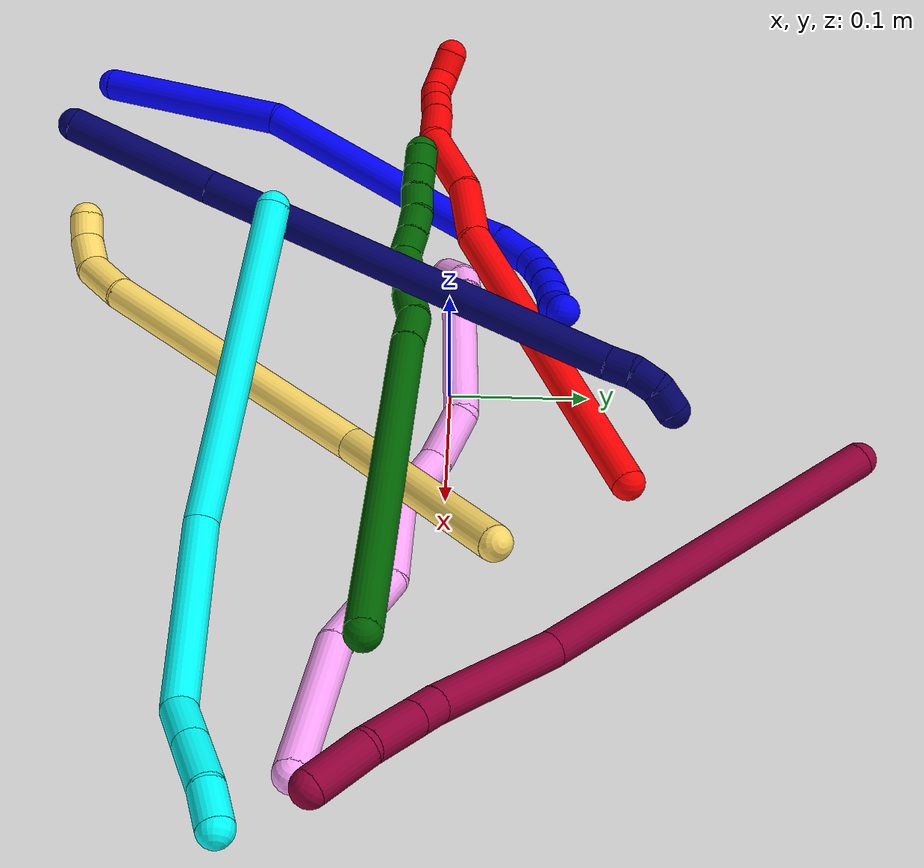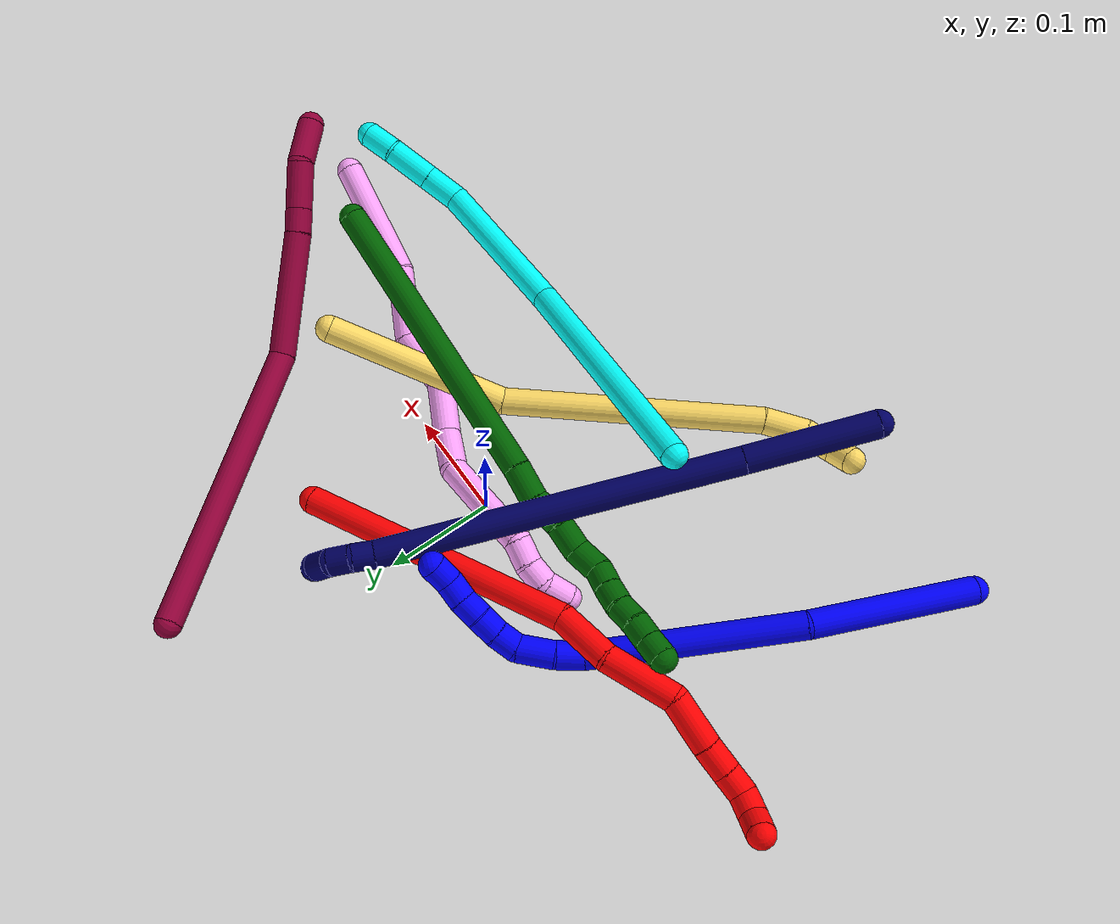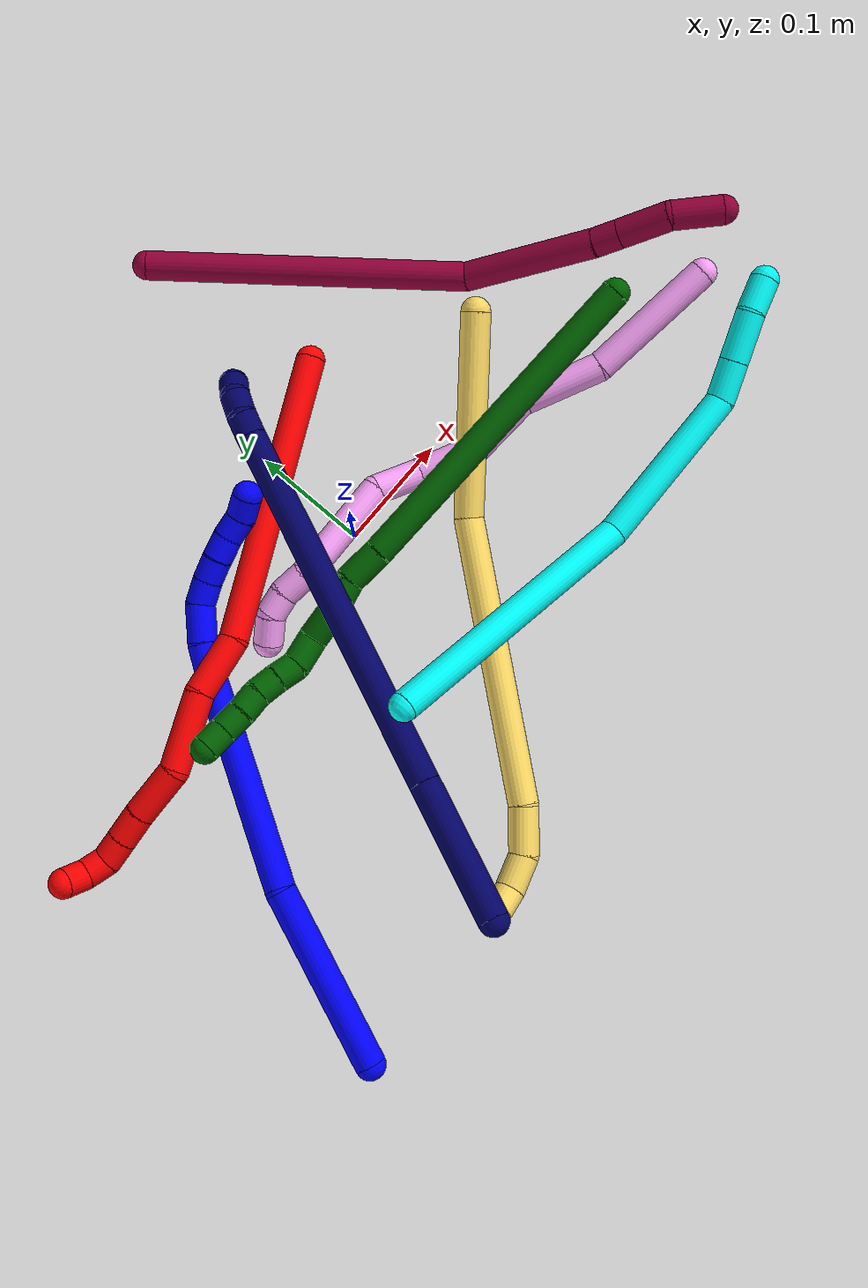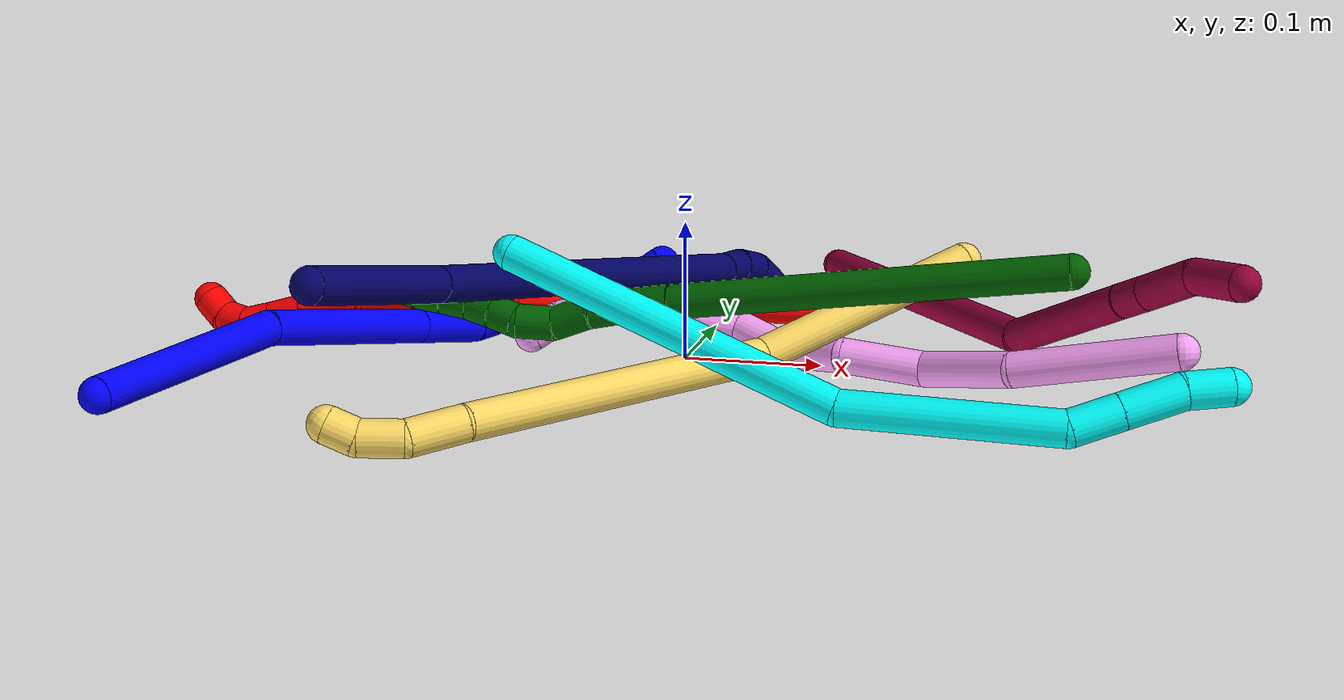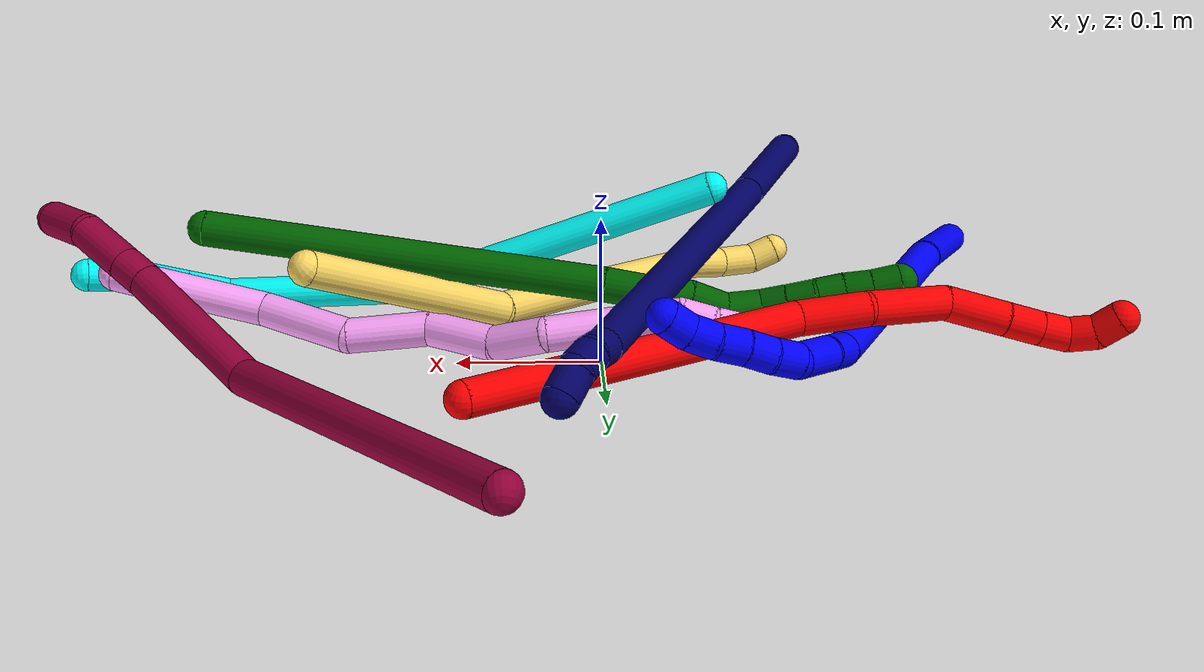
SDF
<sdf version="1.7">
 <world name="default">
  <plugin name="TubeGeneratorPlugin" filename="libtube_generator_plugin.so"/>
  <model name="photoneo_s_sensor">
   <static>1</static>
   <pose>0 0 2 1.57079 1.57079 3.14159</pose>
   <link name="link">
    <inertial><mass>0.1</mass></inertial>
    <sensor name="sensor" type="depth">
     <update_rate>30</update_rate>
     <camera>
      <horizontal_fov>1.22</horizontal_fov>
      <image><width>1920</width><height>1200</height><format>B8G8R8</format></image>
      <clip><near>0.1</near><far>4</far></clip>
      <depth_camera><output>points</output></depth_camera>
     </camera>
     <plugin name="camera_plugin" filename="libgazebo_ros_depth_camera.so">
      <baseline>0.2</baseline>
      <alwaysOn>1</alwaysOn>
      <updateRate>0.0</updateRate>
      <cameraName>camera_ir</cameraName>
      <imageTopicName>/camera/color/image_raw</imageTopicName>
      <cameraInfoTopicName>/camera/color/camera_info</cameraInfoTopicName>
      <depthImageTopicName>/camera/depth/image_raw</depthImageTopicName>
      <depthImageCameraInfoTopicName>/camera/depth/camera_info</depthImageCameraInfoTopicName>
      <pointCloudTopicName>/camera/depth/points</pointCloudTopicName>
      <frameName>fr_optical</frameName>
      <pointCloudCutoff>0.1</pointCloudCutoff>
      <pointCloudCutoffMax>2.0</pointCloudCutoffMax>
      <distortionK1>0</distortionK1>
      <distortionK2>0</distortionK2>
      <distortionK3>0</distortionK3>
      <distortionT1>0</distortionT1>
      <distortionT2>0</distortionT2>
      <CxPrime>0</CxPrime>
      <Cx>0</Cx>
      <Cy>0</Cy>
      <focalLength>0</focalLength>
      <hackBaseline>0</hackBaseline>
     </plugin>
    </sensor>
   </link>
  </model>
  <gravity>0 0 -9.8</gravity>
  <magnetic_field>6e-06 2.3e-05 -4.2e-05</magnetic_field>
  <atmosphere type="adiabatic"/>
  <physics name="default_physics" default="0" type="ode">
   <max_step_size>0.003</max_step_size>
   <real_time_factor>1</real_time_factor>
   <real_time_update_rate>1000</real_time_update_rate>
   <max_contacts>10000</max_contacts>
   <ode>
    <solver>
     <type>quick</type>
     <iters>100</iters>
     <sor>1.3</sor>
     <use_dynamic_moi_rescaling>0</use_dynamic_moi_rescaling>
    </solver>
    <constraints>
     <contact_max_correcting_vel>0</contact_max_correcting_vel>
     <contact_surface_layer>0.001</contact_surface_layer>
     <cfm>0</cfm>
     <erp>0.2</erp>
    </constraints>
   </ode>
  </physics>
  <scene><ambient>0.4 0.4 0.4 1</ambient><background>0.7 0.7 0.7 1</background><shadows>0</shadows></scene>
  <audio><device>default</device></audio>
  <spherical_coordinates>
   <surface_model>EARTH_WGS84</surface_model>
   <latitude_deg>0</latitude_deg>
   <longitude_deg>0</longitude_deg>
   <elevation>0</elevation>
   <heading_deg>0</heading_deg>
  </spherical_coordinates>
  <model name="bin">
   <static>1</static>
   <link name="bottom">
    <collision name="collision-bottom">
     <pose>0 0 -0.01 0 -0 0</pose>
     <geometry><box><size>0.8 0.6 0.02</size></box></geometry>
     <surface>
      <friction><ode><mu>100</mu><mu2>100</mu2></ode></friction>
      <contact><collide_bitmask>65535</collide_bitmask></contact>
     </surface>
    </collision>
   </link>
   <link name="west_wall">
    <collision name="collision-west_wall">
     <pose>-0.41 0 0.1 0 -0 0</pose>
     <geometry><box><size>0.02 0.6 0.2</size></box></geometry>
     <surface>
      <friction><ode><mu>100</mu><mu2>100</mu2></ode></friction>
      <contact><collide_bitmask>65535</collide_bitmask></contact>
     </surface>
    </collision>
   </link>
   <link name="east_wall">
    <collision name="collision-east_wall">
     <pose>0.41 0 0.1 0 -0 0</pose>
     <geometry><box><size>0.02 0.6 0.2</size></box></geometry>
     <surface>
      <friction><ode><mu>100</mu><mu2>100</mu2></ode></friction>
      <contact><collide_bitmask>65535</collide_bitmask></contact>
     </surface>
    </collision>
   </link>
   <link name="south_wall">
    <collision name="collision-south_wall">
     <pose>0 -0.31 0.1 0 -0 0</pose>
     <geometry><box><size>0.8 0.02 0.2</size></box></geometry>
     <surface>
      <friction><ode><mu>100</mu><mu2>100</mu2></ode></friction>
      <contact><collide_bitmask>65535</collide_bitmask></contact>
     </surface>
    </collision>
   </link>
   <link name="north_wall">
    <collision name="collision-north_wall">
     <pose>0 0.31 0.1 0 -0 0</pose>
     <geometry><box><size>0.8 0.02 0.2</size></box></geometry>
     <surface>
      <friction><ode><mu>100</mu><mu2>100</mu2></ode></friction>
      <contact><collide_bitmask>65535</collide_bitmask></contact>
     </surface>
    </collision>
   </link>
  </model>
  <model name="1">
   <static>0</static>
   <link name="1">
    <collision name="collision-cylinder-e_1_1_4">
     <pose>0.00219 0.005585 -0.075692 -3.06794 0.028842 -0.746268</pose>
     <geometry><cylinder><radius>0.0125</radius><length>0.151858</length></cylinder></geometry>
     <surface>
      <friction><ode><mu>1.16</mu><mu2>1.16</mu2><slip1>0</slip1><slip2>0</slip2></ode></friction>
      <contact><ode><kp>1e+06</kp><kd>1</kd><max_vel>0</max_vel><min_depth>0.001</min_depth></ode></contact>
     </surface>
    </collision>
    <visual name="visual-cylinder-e_1_1_4">
     <pose>0.00219 0.005585 -0.075692 -3.06794 0.028842 -0.746268</pose>
     <geometry><cylinder><radius>0.0125</radius><length>0.151858</length></cylinder></geometry>
     <material><ambient>0 0 1 1</ambient></material>
    </visual>
    <collision name="collision-cylinder-e_2_4_5">
     <pose>0.018191 0.00064 -0.21612 2.98035 0.207553 1.82202</pose>
     <geometry><cylinder><radius>0.0125</radius><length>0.134052</length></cylinder></geometry>
     <surface>
      <friction><ode><mu>1.16</mu><mu2>1.16</mu2><slip1>0</slip1><slip2>0</slip2></ode></friction>
      <contact><ode><kp>1e+06</kp><kd>1</kd><max_vel>0</max_vel><min_depth>0.001</min_depth></ode></contact>
     </surface>
    </collision>
    <visual name="visual-cylinder-e_2_4_5">
     <pose>0.018191 0.00064 -0.21612 2.98035 0.207553 1.82202</pose>
     <geometry><cylinder><radius>0.0125</radius><length>0.134052</length></cylinder></geometry>
     <material><ambient>0 0 1 1</ambient></material>
    </visual>
    <collision name="collision-cylinder-e_3_5_6">
     <pose>0.037697 -0.014154 -0.307388 2.98225 0.208814 1.83939</pose>
     <geometry><cylinder><radius>0.0125</radius><length>0.054936</length></cylinder></geometry>
     <surface>
      <friction><ode><mu>1.16</mu><mu2>1.16</mu2><slip1>0</slip1><slip2>0</slip2></ode></friction>
      <contact><ode><kp>1e+06</kp><kd>1</kd><max_vel>0</max_vel><min_depth>0.001</min_depth></ode></contact>
     </surface>
    </collision>
    <visual name="visual-cylinder-e_3_5_6">
     <pose>0.037697 -0.014154 -0.307388 2.98225 0.208814 1.83939</pose>
     <geometry><cylinder><radius>0.0125</radius><length>0.054936</length></cylinder></geometry>
     <material><ambient>0 0 1 1</ambient></material>
    </visual>
    <collision name="collision-cylinder-e_4_6_7">
     <pose>0.046482 -0.016706 -0.346055 -3.00151 0.247018 -2.11281</pose>
     <geometry><cylinder><radius>0.0125</radius><length>0.025281</length></cylinder></geometry>
     <surface>
      <friction><ode><mu>1.16</mu><mu2>1.16</mu2><slip1>0</slip1><slip2>0</slip2></ode></friction>
      <contact><ode><kp>1e+06</kp><kd>1</kd><max_vel>0</max_vel><min_depth>0.001</min_depth></ode></contact>
     </surface>
    </collision>
    <visual name="visual-cylinder-e_4_6_7">
     <pose>0.046482 -0.016706 -0.346055 -3.00151 0.247018 -2.11281</pose>
     <geometry><cylinder><radius>0.0125</radius><length>0.025281</length></cylinder></geometry>
     <material><ambient>0 0 1 1</ambient></material>
    </visual>
    <collision name="collision-cylinder-e_5_7_8">
     <pose>0.056518 -0.013512 -0.372888 -3.04106 0.439521 -2.69854</pose>
     <geometry><cylinder><radius>0.0125</radius><length>0.032644</length></cylinder></geometry>
     <surface>
      <friction><ode><mu>1.16</mu><mu2>1.16</mu2><slip1>0</slip1><slip2>0</slip2></ode></friction>
      <contact><ode><kp>1e+06</kp><kd>1</kd><max_vel>0</max_vel><min_depth>0.001</min_depth></ode></contact>
     </surface>
    </collision>
    <visual name="visual-cylinder-e_5_7_8">
     <pose>0.056518 -0.013512 -0.372888 -3.04106 0.439521 -2.69854</pose>
     <geometry><cylinder><radius>0.0125</radius><length>0.032644</length></cylinder></geometry>
     <material><ambient>0 0 1 1</ambient></material>
    </visual>
    <collision name="collision-cylinder-e_6_8_9">
     <pose>0.070556 -0.0082 -0.394276 -2.62172 0.743742 -1.94463</pose>
     <geometry><cylinder><radius>0.0125</radius><length>0.020954</length></cylinder></geometry>
     <surface>
      <friction><ode><mu>1.16</mu><mu2>1.16</mu2><slip1>0</slip1><slip2>0</slip2></ode></friction>
      <contact><ode><kp>1e+06</kp><kd>1</kd><max_vel>0</max_vel><min_depth>0.001</min_depth></ode></contact>
     </surface>
    </collision>
    <visual name="visual-cylinder-e_6_8_9">
     <pose>0.070556 -0.0082 -0.394276 -2.62172 0.743742 -1.94463</pose>
     <geometry><cylinder><radius>0.0125</radius><length>0.020954</length></cylinder></geometry>
     <material><ambient>0 0 1 1</ambient></material>
    </visual>
    <collision name="collision-cylinder-e_7_9_10">
     <pose>0.084918 0.00016 -0.406292 -2.4367 0.804859 -1.71637</pose>
     <geometry><cylinder><radius>0.0125</radius><length>0.020168</length></cylinder></geometry>
     <surface>
      <friction><ode><mu>1.16</mu><mu2>1.16</mu2><slip1>0</slip1><slip2>0</slip2></ode></friction>
      <contact><ode><kp>1e+06</kp><kd>1</kd><max_vel>0</max_vel><min_depth>0.001</min_depth></ode></contact>
     </surface>
    </collision>
    <visual name="visual-cylinder-e_7_9_10">
     <pose>0.084918 0.00016 -0.406292 -2.4367 0.804859 -1.71637</pose>
     <geometry><cylinder><radius>0.0125</radius><length>0.020168</length></cylinder></geometry>
     <material><ambient>0 0 1 1</ambient></material>
    </visual>
    <collision name="collision-cylinder-e_8_10_11">
     <pose>0.099942 0.008403 -0.416784 -2.51842 0.883781 -1.94616</pose>
     <geometry><cylinder><radius>0.0125</radius><length>0.020064</length></cylinder></geometry>
     <surface>
      <friction><ode><mu>1.16</mu><mu2>1.16</mu2><slip1>0</slip1><slip2>0</slip2></ode></friction>
      <contact><ode><kp>1e+06</kp><kd>1</kd><max_vel>0</max_vel><min_depth>0.001</min_depth></ode></contact>
     </surface>
    </collision>
    <visual name="visual-cylinder-e_8_10_11">
     <pose>0.099942 0.008403 -0.416784 -2.51842 0.883781 -1.94616</pose>
     <geometry><cylinder><radius>0.0125</radius><length>0.020064</length></cylinder></geometry>
     <material><ambient>0 0 1 1</ambient></material>
    </visual>
    <collision name="collision-cylinder-e_9_11_12">
     <pose>0.115711 0.01677 -0.425735 -2.25349 0.928219 -1.62166</pose>
     <geometry><cylinder><radius>0.0125</radius><length>0.020019</length></cylinder></geometry>
     <surface>
      <friction><ode><mu>1.16</mu><mu2>1.16</mu2><slip1>0</slip1><slip2>0</slip2></ode></friction>
      <contact><ode><kp>1e+06</kp><kd>1</kd><max_vel>0</max_vel><min_depth>0.001</min_depth></ode></contact>
     </surface>
    </collision>
    <visual name="visual-cylinder-e_9_11_12">
     <pose>0.115711 0.01677 -0.425735 -2.25349 0.928219 -1.62166</pose>
     <geometry><cylinder><radius>0.0125</radius><length>0.020019</length></cylinder></geometry>
     <material><ambient>0 0 1 1</ambient></material>
    </visual>
    <collision name="collision-cylinder-e_10_12_2">
     <pose>0.12928 0.027926 -0.434724 -2.24594 0.588289 -1.12525</pose>
     <geometry><cylinder><radius>0.0125</radius><length>0.020023</length></cylinder></geometry>
     <surface>
      <friction><ode><mu>1.16</mu><mu2>1.16</mu2><slip1>0</slip1><slip2>0</slip2></ode></friction>
      <contact><ode><kp>1e+06</kp><kd>1</kd><max_vel>0</max_vel><min_depth>0.001</min_depth></ode></contact>
     </surface>
    </collision>
    <visual name="visual-cylinder-e_10_12_2">
     <pose>0.12928 0.027926 -0.434724 -2.24594 0.588289 -1.12525</pose>
     <geometry><cylinder><radius>0.0125</radius><length>0.020023</length></cylinder></geometry>
     <material><ambient>0 0 1 1</ambient></material>
    </visual>
    <collision name="collision-sphere-2">
     <pose>0.134836 0.034427 -0.43993 0 -0 0</pose>
     <geometry><sphere><radius>0.0125</radius></sphere></geometry>
     <surface>
      <friction><ode><mu>1.16</mu><mu2>1.16</mu2><slip1>0</slip1><slip2>0</slip2></ode></friction>
      <contact><ode><kp>1e+06</kp><kd>1</kd><max_vel>0</max_vel><min_depth>0.001</min_depth></ode></contact>
     </surface>
    </collision>
    <visual name="visual-sphere-2">
     <pose>0.134836 0.034427 -0.43993 0 -0 0</pose>
     <geometry><sphere><radius>0.0125</radius></sphere></geometry>
     <material><ambient>0 0 1 1</ambient></material>
    </visual>
    <collision name="collision-sphere-12">
     <pose>0.123725 0.021424 -0.429519 0 -0 0</pose>
     <geometry><sphere><radius>0.0125</radius></sphere></geometry>
     <surface>
      <friction><ode><mu>1.16</mu><mu2>1.16</mu2><slip1>0</slip1><slip2>0</slip2></ode></friction>
      <contact><ode><kp>1e+06</kp><kd>1</kd><max_vel>0</max_vel><min_depth>0.001</min_depth></ode></contact>
     </surface>
    </collision>
    <visual name="visual-sphere-12">
     <pose>0.123725 0.021424 -0.429519 0 -0 0</pose>
     <geometry><sphere><radius>0.0125</radius></sphere></geometry>
     <material><ambient>0 0 1 1</ambient></material>
    </visual>
    <collision name="collision-sphere-11">
     <pose>0.107698 0.012116 -0.42195 0 -0 0</pose>
     <geometry><sphere><radius>0.0125</radius></sphere></geometry>
     <surface>
      <friction><ode><mu>1.16</mu><mu2>1.16</mu2><slip1>0</slip1><slip2>0</slip2></ode></friction>
      <contact><ode><kp>1e+06</kp><kd>1</kd><max_vel>0</max_vel><min_depth>0.001</min_depth></ode></contact>
     </surface>
    </collision>
    <visual name="visual-sphere-11">
     <pose>0.107698 0.012116 -0.42195 0 -0 0</pose>
     <geometry><sphere><radius>0.0125</radius></sphere></geometry>
     <material><ambient>0 0 1 1</ambient></material>
    </visual>
    <collision name="collision-sphere-10">
     <pose>0.092186 0.00469 -0.411617 0 -0 0</pose>
     <geometry><sphere><radius>0.0125</radius></sphere></geometry>
     <surface>
      <friction><ode><mu>1.16</mu><mu2>1.16</mu2><slip1>0</slip1><slip2>0</slip2></ode></friction>
      <contact><ode><kp>1e+06</kp><kd>1</kd><max_vel>0</max_vel><min_depth>0.001</min_depth></ode></contact>
     </surface>
    </collision>
    <visual name="visual-sphere-10">
     <pose>0.092186 0.00469 -0.411617 0 -0 0</pose>
     <geometry><sphere><radius>0.0125</radius></sphere></geometry>
     <material><ambient>0 0 1 1</ambient></material>
    </visual>
    <collision name="collision-sphere-9">
     <pose>0.07765 -0.004369 -0.400968 0 -0 0</pose>
     <geometry><sphere><radius>0.0125</radius></sphere></geometry>
     <surface>
      <friction><ode><mu>1.16</mu><mu2>1.16</mu2><slip1>0</slip1><slip2>0</slip2></ode></friction>
      <contact><ode><kp>1e+06</kp><kd>1</kd><max_vel>0</max_vel><min_depth>0.001</min_depth></ode></contact>
     </surface>
    </collision>
    <visual name="visual-sphere-9">
     <pose>0.07765 -0.004369 -0.400968 0 -0 0</pose>
     <geometry><sphere><radius>0.0125</radius></sphere></geometry>
     <material><ambient>0 0 1 1</ambient></material>
    </visual>
    <collision name="collision-sphere-4">
     <pose>0.004379 0.011169 -0.151384 0 -0 0</pose>
     <geometry><sphere><radius>0.0125</radius></sphere></geometry>
     <surface>
      <friction><ode><mu>1.16</mu><mu2>1.16</mu2><slip1>0</slip1><slip2>0</slip2></ode></friction>
      <contact><ode><kp>1e+06</kp><kd>1</kd><max_vel>0</max_vel><min_depth>0.001</min_depth></ode></contact>
     </surface>
    </collision>
    <visual name="visual-sphere-4">
     <pose>0.004379 0.011169 -0.151384 0 -0 0</pose>
     <geometry><sphere><radius>0.0125</radius></sphere></geometry>
     <material><ambient>0 0 1 1</ambient></material>
    </visual>
    <collision name="collision-sphere-1">
     <geometry><sphere><radius>0.0125</radius></sphere></geometry>
     <surface>
      <friction><ode><mu>1.16</mu><mu2>1.16</mu2><slip1>0</slip1><slip2>0</slip2></ode></friction>
      <contact><ode><kp>1e+06</kp><kd>1</kd><max_vel>0</max_vel><min_depth>0.001</min_depth></ode></contact>
     </surface>
    </collision>
    <visual name="visual-sphere-1">
     <geometry><sphere><radius>0.0125</radius></sphere></geometry>
     <material><ambient>0 0 1 1</ambient></material>
    </visual>
    <collision name="collision-sphere-8">
     <pose>0.063463 -0.01203 -0.387584 0 -0 0</pose>
     <geometry><sphere><radius>0.0125</radius></sphere></geometry>
     <surface>
      <friction><ode><mu>1.16</mu><mu2>1.16</mu2><slip1>0</slip1><slip2>0</slip2></ode></friction>
      <contact><ode><kp>1e+06</kp><kd>1</kd><max_vel>0</max_vel><min_depth>0.001</min_depth></ode></contact>
     </surface>
    </collision>
    <visual name="visual-sphere-8">
     <pose>0.063463 -0.01203 -0.387584 0 -0 0</pose>
     <geometry><sphere><radius>0.0125</radius></sphere></geometry>
     <material><ambient>0 0 1 1</ambient></material>
    </visual>
    <collision name="collision-sphere-5">
     <pose>0.032003 -0.00989 -0.280857 0 -0 0</pose>
     <geometry><sphere><radius>0.0125</radius></sphere></geometry>
     <surface>
      <friction><ode><mu>1.16</mu><mu2>1.16</mu2><slip1>0</slip1><slip2>0</slip2></ode></friction>
      <contact><ode><kp>1e+06</kp><kd>1</kd><max_vel>0</max_vel><min_depth>0.001</min_depth></ode></contact>
     </surface>
    </collision>
    <visual name="visual-sphere-5">
     <pose>0.032003 -0.00989 -0.280857 0 -0 0</pose>
     <geometry><sphere><radius>0.0125</radius></sphere></geometry>
     <material><ambient>0 0 1 1</ambient></material>
    </visual>
    <collision name="collision-sphere-6">
     <pose>0.043391 -0.018418 -0.333919 0 -0 0</pose>
     <geometry><sphere><radius>0.0125</radius></sphere></geometry>
     <surface>
      <friction><ode><mu>1.16</mu><mu2>1.16</mu2><slip1>0</slip1><slip2>0</slip2></ode></friction>
      <contact><ode><kp>1e+06</kp><kd>1</kd><max_vel>0</max_vel><min_depth>0.001</min_depth></ode></contact>
     </surface>
    </collision>
    <visual name="visual-sphere-6">
     <pose>0.043391 -0.018418 -0.333919 0 -0 0</pose>
     <geometry><sphere><radius>0.0125</radius></sphere></geometry>
     <material><ambient>0 0 1 1</ambient></material>
    </visual>
    <collision name="collision-sphere-7">
     <pose>0.049573 -0.014995 -0.358192 0 -0 0</pose>
     <geometry><sphere><radius>0.0125</radius></sphere></geometry>
     <surface>
      <friction><ode><mu>1.16</mu><mu2>1.16</mu2><slip1>0</slip1><slip2>0</slip2></ode></friction>
      <contact><ode><kp>1e+06</kp><kd>1</kd><max_vel>0</max_vel><min_depth>0.001</min_depth></ode></contact>
     </surface>
    </collision>
    <visual name="visual-sphere-7">
     <pose>0.049573 -0.014995 -0.358192 0 -0 0</pose>
     <geometry><sphere><radius>0.0125</radius></sphere></geometry>
     <material><ambient>0 0 1 1</ambient></material>
    </visual>
    <inertial>
     <pose>0.035927 0.000375 -0.240639 0 -0 0</pose>
     <mass>0.5</mass>
     <inertia>
      <ixx>0.00017</ixx>
      <ixy>0</ixy>
      <ixz>0</ixz>
      <iyy>-0.000144</iyy>
      <iyz>0</iyz>
      <izz>-8.7e-05</izz>
     </inertia>
    </inertial>
   </link>
   <pose>-0.314056 -0.288502 0.029176 1.59226 0.15198 -0.334648</pose>
  </model>
  <model name="2">
   <static>0</static>
   <link name="2">
    <collision name="collision-cylinder-e_1_1_4">
     <pose>-0.10783 0.06316 -0.007631 -1.69103 -1.03777 1.14461</pose>
     <geometry><cylinder><radius>0.0125</radius><length>0.250397</length></cylinder></geometry>
     <surface>
      <friction><ode><mu>1.16</mu><mu2>1.16</mu2><slip1>0</slip1><slip2>0</slip2></ode></friction>
      <contact><ode><kp>1e+06</kp><kd>1</kd><max_vel>0</max_vel><min_depth>0.001</min_depth></ode></contact>
     </surface>
    </collision>
    <visual name="visual-cylinder-e_1_1_4">
     <pose>-0.10783 0.06316 -0.007631 -1.69103 -1.03777 1.14461</pose>
     <geometry><cylinder><radius>0.0125</radius><length>0.250397</length></cylinder></geometry>
     <material><ambient>1 0 0 1</ambient></material>
    </visual>
    <collision name="collision-cylinder-e_2_4_5">
     <pose>-0.240329 0.132167 -0.01852 -2.07923 -1.30583 1.83154</pose>
     <geometry><cylinder><radius>0.0125</radius><length>0.051122</length></cylinder></geometry>
     <surface>
      <friction><ode><mu>1.16</mu><mu2>1.16</mu2><slip1>0</slip1><slip2>0</slip2></ode></friction>
      <contact><ode><kp>1e+06</kp><kd>1</kd><max_vel>0</max_vel><min_depth>0.001</min_depth></ode></contact>
     </surface>
    </collision>
    <visual name="visual-cylinder-e_2_4_5">
     <pose>-0.240329 0.132167 -0.01852 -2.07923 -1.30583 1.83154</pose>
     <geometry><cylinder><radius>0.0125</radius><length>0.051122</length></cylinder></geometry>
     <material><ambient>1 0 0 1</ambient></material>
    </visual>
    <collision name="collision-cylinder-e_3_5_6">
     <pose>-0.294226 0.151974 -0.020375 -1.47059 -1.12325 1.03481</pose>
     <geometry><cylinder><radius>0.0125</radius><length>0.064844</length></cylinder></geometry>
     <surface>
      <friction><ode><mu>1.16</mu><mu2>1.16</mu2><slip1>0</slip1><slip2>0</slip2></ode></friction>
      <contact><ode><kp>1e+06</kp><kd>1</kd><max_vel>0</max_vel><min_depth>0.001</min_depth></ode></contact>
     </surface>
    </collision>
    <visual name="visual-cylinder-e_3_5_6">
     <pose>-0.294226 0.151974 -0.020375 -1.47059 -1.12325 1.03481</pose>
     <geometry><cylinder><radius>0.0125</radius><length>0.064844</length></cylinder></geometry>
     <material><ambient>1 0 0 1</ambient></material>
    </visual>
    <collision name="collision-cylinder-e_4_6_7">
     <pose>-0.345849 0.165868 -0.014668 0.015376 -1.3809 -0.012702</pose>
     <geometry><cylinder><radius>0.0125</radius><length>0.045607</length></cylinder></geometry>
     <surface>
      <friction><ode><mu>1.16</mu><mu2>1.16</mu2><slip1>0</slip1><slip2>0</slip2></ode></friction>
      <contact><ode><kp>1e+06</kp><kd>1</kd><max_vel>0</max_vel><min_depth>0.001</min_depth></ode></contact>
     </surface>
    </collision>
    <visual name="visual-cylinder-e_4_6_7">
     <pose>-0.345849 0.165868 -0.014668 0.015376 -1.3809 -0.012702</pose>
     <geometry><cylinder><radius>0.0125</radius><length>0.045607</length></cylinder></geometry>
     <material><ambient>1 0 0 1</ambient></material>
    </visual>
    <collision name="collision-cylinder-e_5_7_8">
     <pose>-0.380903 0.16655 -0.007605 -0.264517 -1.34875 0.211901</pose>
     <geometry><cylinder><radius>0.0125</radius><length>0.025959</length></cylinder></geometry>
     <surface>
      <friction><ode><mu>1.16</mu><mu2>1.16</mu2><slip1>0</slip1><slip2>0</slip2></ode></friction>
      <contact><ode><kp>1e+06</kp><kd>1</kd><max_vel>0</max_vel><min_depth>0.001</min_depth></ode></contact>
     </surface>
    </collision>
    <visual name="visual-cylinder-e_5_7_8">
     <pose>-0.380903 0.16655 -0.007605 -0.264517 -1.34875 0.211901</pose>
     <geometry><cylinder><radius>0.0125</radius><length>0.025959</length></cylinder></geometry>
     <material><ambient>1 0 0 1</ambient></material>
    </visual>
    <collision name="collision-cylinder-e_6_8_9">
     <pose>-0.404302 0.168039 -0.002919 -0.367913 -1.38085 0.305003</pose>
     <geometry><cylinder><radius>0.0125</radius><length>0.021869</length></cylinder></geometry>
     <surface>
      <friction><ode><mu>1.16</mu><mu2>1.16</mu2><slip1>0</slip1><slip2>0</slip2></ode></friction>
      <contact><ode><kp>1e+06</kp><kd>1</kd><max_vel>0</max_vel><min_depth>0.001</min_depth></ode></contact>
     </surface>
    </collision>
    <visual name="visual-cylinder-e_6_8_9">
     <pose>-0.404302 0.168039 -0.002919 -0.367913 -1.38085 0.305003</pose>
     <geometry><cylinder><radius>0.0125</radius><length>0.021869</length></cylinder></geometry>
     <material><ambient>1 0 0 1</ambient></material>
    </visual>
    <collision name="collision-cylinder-e_7_9_10">
     <pose>-0.424554 0.166933 -0.003724 2.54636 -1.23714 -2.3278</pose>
     <geometry><cylinder><radius>0.0125</radius><length>0.020138</length></cylinder></geometry>
     <surface>
      <friction><ode><mu>1.16</mu><mu2>1.16</mu2><slip1>0</slip1><slip2>0</slip2></ode></friction>
      <contact><ode><kp>1e+06</kp><kd>1</kd><max_vel>0</max_vel><min_depth>0.001</min_depth></ode></contact>
     </surface>
    </collision>
    <visual name="visual-cylinder-e_7_9_10">
     <pose>-0.424554 0.166933 -0.003724 2.54636 -1.23714 -2.3278</pose>
     <geometry><cylinder><radius>0.0125</radius><length>0.020138</length></cylinder></geometry>
     <material><ambient>1 0 0 1</ambient></material>
    </visual>
    <collision name="collision-cylinder-e_8_10_2">
     <pose>-0.441073 0.163361 -0.013425 2.89933 -0.772998 -2.56032</pose>
     <geometry><cylinder><radius>0.0125</radius><length>0.020063</length></cylinder></geometry>
     <surface>
      <friction><ode><mu>1.16</mu><mu2>1.16</mu2><slip1>0</slip1><slip2>0</slip2></ode></friction>
      <contact><ode><kp>1e+06</kp><kd>1</kd><max_vel>0</max_vel><min_depth>0.001</min_depth></ode></contact>
     </surface>
    </collision>
    <visual name="visual-cylinder-e_8_10_2">
     <pose>-0.441073 0.163361 -0.013425 2.89933 -0.772998 -2.56032</pose>
     <geometry><cylinder><radius>0.0125</radius><length>0.020063</length></cylinder></geometry>
     <material><ambient>1 0 0 1</ambient></material>
    </visual>
    <collision name="collision-sphere-2">
     <pose>-0.448078 0.161639 -0.020397 0 -0 0</pose>
     <geometry><sphere><radius>0.0125</radius></sphere></geometry>
     <surface>
      <friction><ode><mu>1.16</mu><mu2>1.16</mu2><slip1>0</slip1><slip2>0</slip2></ode></friction>
      <contact><ode><kp>1e+06</kp><kd>1</kd><max_vel>0</max_vel><min_depth>0.001</min_depth></ode></contact>
     </surface>
    </collision>
    <visual name="visual-sphere-2">
     <pose>-0.448078 0.161639 -0.020397 0 -0 0</pose>
     <geometry><sphere><radius>0.0125</radius></sphere></geometry>
     <material><ambient>1 0 0 1</ambient></material>
    </visual>
    <collision name="collision-sphere-10">
     <pose>-0.434068 0.165084 -0.006454 0 -0 0</pose>
     <geometry><sphere><radius>0.0125</radius></sphere></geometry>
     <surface>
      <friction><ode><mu>1.16</mu><mu2>1.16</mu2><slip1>0</slip1><slip2>0</slip2></ode></friction>
      <contact><ode><kp>1e+06</kp><kd>1</kd><max_vel>0</max_vel><min_depth>0.001</min_depth></ode></contact>
     </surface>
    </collision>
    <visual name="visual-sphere-10">
     <pose>-0.434068 0.165084 -0.006454 0 -0 0</pose>
     <geometry><sphere><radius>0.0125</radius></sphere></geometry>
     <material><ambient>1 0 0 1</ambient></material>
    </visual>
    <collision name="collision-sphere-9">
     <pose>-0.41504 0.168782 -0.000993 0 -0 0</pose>
     <geometry><sphere><radius>0.0125</radius></sphere></geometry>
     <surface>
      <friction><ode><mu>1.16</mu><mu2>1.16</mu2><slip1>0</slip1><slip2>0</slip2></ode></friction>
      <contact><ode><kp>1e+06</kp><kd>1</kd><max_vel>0</max_vel><min_depth>0.001</min_depth></ode></contact>
     </surface>
    </collision>
    <visual name="visual-sphere-9">
     <pose>-0.41504 0.168782 -0.000993 0 -0 0</pose>
     <geometry><sphere><radius>0.0125</radius></sphere></geometry>
     <material><ambient>1 0 0 1</ambient></material>
    </visual>
    <collision name="collision-sphere-4">
     <pose>-0.21566 0.12632 -0.015262 0 -0 0</pose>
     <geometry><sphere><radius>0.0125</radius></sphere></geometry>
     <surface>
      <friction><ode><mu>1.16</mu><mu2>1.16</mu2><slip1>0</slip1><slip2>0</slip2></ode></friction>
      <contact><ode><kp>1e+06</kp><kd>1</kd><max_vel>0</max_vel><min_depth>0.001</min_depth></ode></contact>
     </surface>
    </collision>
    <visual name="visual-sphere-4">
     <pose>-0.21566 0.12632 -0.015262 0 -0 0</pose>
     <geometry><sphere><radius>0.0125</radius></sphere></geometry>
     <material><ambient>1 0 0 1</ambient></material>
    </visual>
    <collision name="collision-sphere-1">
     <geometry><sphere><radius>0.0125</radius></sphere></geometry>
     <surface>
      <friction><ode><mu>1.16</mu><mu2>1.16</mu2><slip1>0</slip1><slip2>0</slip2></ode></friction>
      <contact><ode><kp>1e+06</kp><kd>1</kd><max_vel>0</max_vel><min_depth>0.001</min_depth></ode></contact>
     </surface>
    </collision>
    <visual name="visual-sphere-1">
     <geometry><sphere><radius>0.0125</radius></sphere></geometry>
     <material><ambient>1 0 0 1</ambient></material>
    </visual>
    <collision name="collision-sphere-8">
     <pose>-0.393564 0.167297 -0.004846 0 -0 0</pose>
     <geometry><sphere><radius>0.0125</radius></sphere></geometry>
     <surface>
      <friction><ode><mu>1.16</mu><mu2>1.16</mu2><slip1>0</slip1><slip2>0</slip2></ode></friction>
      <contact><ode><kp>1e+06</kp><kd>1</kd><max_vel>0</max_vel><min_depth>0.001</min_depth></ode></contact>
     </surface>
    </collision>
    <visual name="visual-sphere-8">
     <pose>-0.393564 0.167297 -0.004846 0 -0 0</pose>
     <geometry><sphere><radius>0.0125</radius></sphere></geometry>
     <material><ambient>1 0 0 1</ambient></material>
    </visual>
    <collision name="collision-sphere-5">
     <pose>-0.264998 0.138014 -0.021779 0 -0 0</pose>
     <geometry><sphere><radius>0.0125</radius></sphere></geometry>
     <surface>
      <friction><ode><mu>1.16</mu><mu2>1.16</mu2><slip1>0</slip1><slip2>0</slip2></ode></friction>
      <contact><ode><kp>1e+06</kp><kd>1</kd><max_vel>0</max_vel><min_depth>0.001</min_depth></ode></contact>
     </surface>
    </collision>
    <visual name="visual-sphere-5">
     <pose>-0.264998 0.138014 -0.021779 0 -0 0</pose>
     <geometry><sphere><radius>0.0125</radius></sphere></geometry>
     <material><ambient>1 0 0 1</ambient></material>
    </visual>
    <collision name="collision-sphere-6">
     <pose>-0.323455 0.165935 -0.018971 0 -0 0</pose>
     <geometry><sphere><radius>0.0125</radius></sphere></geometry>
     <surface>
      <friction><ode><mu>1.16</mu><mu2>1.16</mu2><slip1>0</slip1><slip2>0</slip2></ode></friction>
      <contact><ode><kp>1e+06</kp><kd>1</kd><max_vel>0</max_vel><min_depth>0.001</min_depth></ode></contact>
     </surface>
    </collision>
    <visual name="visual-sphere-6">
     <pose>-0.323455 0.165935 -0.018971 0 -0 0</pose>
     <geometry><sphere><radius>0.0125</radius></sphere></geometry>
     <material><ambient>1 0 0 1</ambient></material>
    </visual>
    <collision name="collision-sphere-7">
     <pose>-0.368242 0.165802 -0.010364 0 -0 0</pose>
     <geometry><sphere><radius>0.0125</radius></sphere></geometry>
     <surface>
      <friction><ode><mu>1.16</mu><mu2>1.16</mu2><slip1>0</slip1><slip2>0</slip2></ode></friction>
      <contact><ode><kp>1e+06</kp><kd>1</kd><max_vel>0</max_vel><min_depth>0.001</min_depth></ode></contact>
     </surface>
    </collision>
    <visual name="visual-sphere-7">
     <pose>-0.368242 0.165802 -0.010364 0 -0 0</pose>
     <geometry><sphere><radius>0.0125</radius></sphere></geometry>
     <material><ambient>1 0 0 1</ambient></material>
    </visual>
    <inertial>
     <pose>-0.220534 0.109257 -0.010907 0 -0 0</pose>
     <mass>0.5</mass>
     <inertia>
      <ixx>0.00087</ixx>
      <ixy>0</ixy>
      <ixz>0</ixz>
      <iyy>0.001645</iyy>
      <iyz>0</iyz>
      <izz>0.000507</izz>
     </inertia>
    </inertial>
   </link>
   <pose>0.089402 0.126246 0.012318 2.94739 -0.08262 -0.037764</pose>
  </model>
  <model name="3">
   <static>0</static>
   <link name="3">
    <collision name="collision-cylinder-e_1_1_4">
     <pose>0.027877 -0.010878 0.118489 0.091551 0.230136 0.010589</pose>
     <geometry><cylinder><radius>0.0125</radius><length>0.244419</length></cylinder></geometry>
     <surface>
      <friction><ode><mu>1.16</mu><mu2>1.16</mu2><slip1>0</slip1><slip2>0</slip2></ode></friction>
      <contact><ode><kp>1e+06</kp><kd>1</kd><max_vel>0</max_vel><min_depth>0.001</min_depth></ode></contact>
     </surface>
    </collision>
    <visual name="visual-cylinder-e_1_1_4">
     <pose>0.027877 -0.010878 0.118489 0.091551 0.230136 0.010589</pose>
     <geometry><cylinder><radius>0.0125</radius><length>0.244419</length></cylinder></geometry>
     <material><ambient>0.003922 1 0.996078 1</ambient></material>
    </visual>
    <collision name="collision-cylinder-e_2_4_5">
     <pose>0.046719 -0.025692 0.309992 0.053844 -0.12295 -0.003315</pose>
     <geometry><cylinder><radius>0.0125</radius><length>0.147352</length></cylinder></geometry>
     <surface>
      <friction><ode><mu>1.16</mu><mu2>1.16</mu2><slip1>0</slip1><slip2>0</slip2></ode></friction>
      <contact><ode><kp>1e+06</kp><kd>1</kd><max_vel>0</max_vel><min_depth>0.001</min_depth></ode></contact>
     </surface>
    </collision>
    <visual name="visual-cylinder-e_2_4_5">
     <pose>0.046719 -0.025692 0.309992 0.053844 -0.12295 -0.003315</pose>
     <geometry><cylinder><radius>0.0125</radius><length>0.147352</length></cylinder></geometry>
     <material><ambient>0.003922 1 0.996078 1</ambient></material>
    </visual>
    <collision name="collision-cylinder-e_3_5_6">
     <pose>0.028772 -0.026774 0.397745 -0.19117 -0.535663 0.05261</pose>
     <geometry><cylinder><radius>0.0125</radius><length>0.034916</length></cylinder></geometry>
     <surface>
      <friction><ode><mu>1.16</mu><mu2>1.16</mu2><slip1>0</slip1><slip2>0</slip2></ode></friction>
      <contact><ode><kp>1e+06</kp><kd>1</kd><max_vel>0</max_vel><min_depth>0.001</min_depth></ode></contact>
     </surface>
    </collision>
    <visual name="visual-cylinder-e_3_5_6">
     <pose>0.028772 -0.026774 0.397745 -0.19117 -0.535663 0.05261</pose>
     <geometry><cylinder><radius>0.0125</radius><length>0.034916</length></cylinder></geometry>
     <material><ambient>0.003922 1 0.996078 1</ambient></material>
    </visual>
    <collision name="collision-cylinder-e_4_6_7">
     <pose>0.008912 -0.020369 0.430608 -0.193549 -0.535142 0.053214</pose>
     <geometry><cylinder><radius>0.0125</radius><length>0.042942</length></cylinder></geometry>
     <surface>
      <friction><ode><mu>1.16</mu><mu2>1.16</mu2><slip1>0</slip1><slip2>0</slip2></ode></friction>
      <contact><ode><kp>1e+06</kp><kd>1</kd><max_vel>0</max_vel><min_depth>0.001</min_depth></ode></contact>
     </surface>
    </collision>
    <visual name="visual-cylinder-e_4_6_7">
     <pose>0.008912 -0.020369 0.430608 -0.193549 -0.535142 0.053214</pose>
     <geometry><cylinder><radius>0.0125</radius><length>0.042942</length></cylinder></geometry>
     <material><ambient>0.003922 1 0.996078 1</ambient></material>
    </visual>
    <collision name="collision-cylinder-e_5_7_2">
     <pose>-0.006669 -0.014187 0.462953 -0.182887 -0.309971 0.028652</pose>
     <geometry><cylinder><radius>0.0125</radius><length>0.030372</length></cylinder></geometry>
     <surface>
      <friction><ode><mu>1.16</mu><mu2>1.16</mu2><slip1>0</slip1><slip2>0</slip2></ode></friction>
      <contact><ode><kp>1e+06</kp><kd>1</kd><max_vel>0</max_vel><min_depth>0.001</min_depth></ode></contact>
     </surface>
    </collision>
    <visual name="visual-cylinder-e_5_7_2">
     <pose>-0.006669 -0.014187 0.462953 -0.182887 -0.309971 0.028652</pose>
     <geometry><cylinder><radius>0.0125</radius><length>0.030372</length></cylinder></geometry>
     <material><ambient>0.003922 1 0.996078 1</ambient></material>
    </visual>
    <collision name="collision-sphere-2">
     <pose>-0.011301 -0.011556 0.477175 0 -0 0</pose>
     <geometry><sphere><radius>0.0125</radius></sphere></geometry>
     <surface>
      <friction><ode><mu>1.16</mu><mu2>1.16</mu2><slip1>0</slip1><slip2>0</slip2></ode></friction>
      <contact><ode><kp>1e+06</kp><kd>1</kd><max_vel>0</max_vel><min_depth>0.001</min_depth></ode></contact>
     </surface>
    </collision>
    <visual name="visual-sphere-2">
     <pose>-0.011301 -0.011556 0.477175 0 -0 0</pose>
     <geometry><sphere><radius>0.0125</radius></sphere></geometry>
     <material><ambient>0.003922 1 0.996078 1</ambient></material>
    </visual>
    <collision name="collision-sphere-7">
     <pose>-0.002037 -0.016817 0.448732 0 -0 0</pose>
     <geometry><sphere><radius>0.0125</radius></sphere></geometry>
     <surface>
      <friction><ode><mu>1.16</mu><mu2>1.16</mu2><slip1>0</slip1><slip2>0</slip2></ode></friction>
      <contact><ode><kp>1e+06</kp><kd>1</kd><max_vel>0</max_vel><min_depth>0.001</min_depth></ode></contact>
     </surface>
    </collision>
    <visual name="visual-sphere-7">
     <pose>-0.002037 -0.016817 0.448732 0 -0 0</pose>
     <geometry><sphere><radius>0.0125</radius></sphere></geometry>
     <material><ambient>0.003922 1 0.996078 1</ambient></material>
    </visual>
    <collision name="collision-sphere-6">
     <pose>0.019862 -0.023922 0.412484 0 -0 0</pose>
     <geometry><sphere><radius>0.0125</radius></sphere></geometry>
     <surface>
      <friction><ode><mu>1.16</mu><mu2>1.16</mu2><slip1>0</slip1><slip2>0</slip2></ode></friction>
      <contact><ode><kp>1e+06</kp><kd>1</kd><max_vel>0</max_vel><min_depth>0.001</min_depth></ode></contact>
     </surface>
    </collision>
    <visual name="visual-sphere-6">
     <pose>0.019862 -0.023922 0.412484 0 -0 0</pose>
     <geometry><sphere><radius>0.0125</radius></sphere></geometry>
     <material><ambient>0.003922 1 0.996078 1</ambient></material>
    </visual>
    <collision name="collision-sphere-5">
     <pose>0.037683 -0.029627 0.383006 0 -0 0</pose>
     <geometry><sphere><radius>0.0125</radius></sphere></geometry>
     <surface>
      <friction><ode><mu>1.16</mu><mu2>1.16</mu2><slip1>0</slip1><slip2>0</slip2></ode></friction>
      <contact><ode><kp>1e+06</kp><kd>1</kd><max_vel>0</max_vel><min_depth>0.001</min_depth></ode></contact>
     </surface>
    </collision>
    <visual name="visual-sphere-5">
     <pose>0.037683 -0.029627 0.383006 0 -0 0</pose>
     <geometry><sphere><radius>0.0125</radius></sphere></geometry>
     <material><ambient>0.003922 1 0.996078 1</ambient></material>
    </visual>
    <collision name="collision-sphere-1">
     <geometry><sphere><radius>0.0125</radius></sphere></geometry>
     <surface>
      <friction><ode><mu>1.16</mu><mu2>1.16</mu2><slip1>0</slip1><slip2>0</slip2></ode></friction>
      <contact><ode><kp>1e+06</kp><kd>1</kd><max_vel>0</max_vel><min_depth>0.001</min_depth></ode></contact>
     </surface>
    </collision>
    <visual name="visual-sphere-1">
     <geometry><sphere><radius>0.0125</radius></sphere></geometry>
     <material><ambient>0.003922 1 0.996078 1</ambient></material>
    </visual>
    <collision name="collision-sphere-4">
     <pose>0.055754 -0.021756 0.236978 0 -0 0</pose>
     <geometry><sphere><radius>0.0125</radius></sphere></geometry>
     <surface>
      <friction><ode><mu>1.16</mu><mu2>1.16</mu2><slip1>0</slip1><slip2>0</slip2></ode></friction>
      <contact><ode><kp>1e+06</kp><kd>1</kd><max_vel>0</max_vel><min_depth>0.001</min_depth></ode></contact>
     </surface>
    </collision>
    <visual name="visual-sphere-4">
     <pose>0.055754 -0.021756 0.236978 0 -0 0</pose>
     <geometry><sphere><radius>0.0125</radius></sphere></geometry>
     <material><ambient>0.003922 1 0.996078 1</ambient></material>
    </visual>
    <inertial>
     <pose>0.029765 -0.01737 0.242156 0 -0 0</pose>
     <mass>0.5</mass>
     <inertia><ixx>0.001491</ixx><ixy>0</ixy><ixz>0</ixz><iyy>0.001521</iyy><iyz>0</iyz><izz>-8e-05</izz></inertia>
    </inertial>
   </link>
   <pose>-0.08828 -0.131343 0.100443 -2.03067 1.1931 -1.97364</pose>
  </model>
  <model name="4">
   <static>0</static>
   <link name="4">
    <collision name="collision-cylinder-e_1_1_4">
     <pose>-0.055822 0.010734 0.007309 -0.973 -1.34223 0.795231</pose>
     <geometry><cylinder><radius>0.0125</radius><length>0.114625</length></cylinder></geometry>
     <surface>
      <friction><ode><mu>1.16</mu><mu2>1.16</mu2><slip1>0</slip1><slip2>0</slip2></ode></friction>
      <contact><ode><kp>1e+06</kp><kd>1</kd><max_vel>0</max_vel><min_depth>0.001</min_depth></ode></contact>
     </surface>
    </collision>
    <visual name="visual-cylinder-e_1_1_4">
     <pose>-0.055822 0.010734 0.007309 -0.973 -1.34223 0.795231</pose>
     <geometry><cylinder><radius>0.0125</radius><length>0.114625</length></cylinder></geometry>
     <material><ambient>1 0.65098 0.996078 1</ambient></material>
    </visual>
    <collision name="collision-cylinder-e_2_4_5">
     <pose>-0.147063 0.016816 0.016264 1.23064 -1.43237 -1.10307</pose>
     <geometry><cylinder><radius>0.0125</radius><length>0.071523</length></cylinder></geometry>
     <surface>
      <friction><ode><mu>1.16</mu><mu2>1.16</mu2><slip1>0</slip1><slip2>0</slip2></ode></friction>
      <contact><ode><kp>1e+06</kp><kd>1</kd><max_vel>0</max_vel><min_depth>0.001</min_depth></ode></contact>
     </surface>
    </collision>
    <visual name="visual-cylinder-e_2_4_5">
     <pose>-0.147063 0.016816 0.016264 1.23064 -1.43237 -1.10307</pose>
     <geometry><cylinder><radius>0.0125</radius><length>0.071523</length></cylinder></geometry>
     <material><ambient>1 0.65098 0.996078 1</ambient></material>
    </visual>
    <collision name="collision-cylinder-e_3_5_6">
     <pose>-0.209808 0.02173 0.013389 -2.0123 -1.20139 1.6492</pose>
     <geometry><cylinder><radius>0.0125</radius><length>0.058603</length></cylinder></geometry>
     <surface>
      <friction><ode><mu>1.16</mu><mu2>1.16</mu2><slip1>0</slip1><slip2>0</slip2></ode></friction>
      <contact><ode><kp>1e+06</kp><kd>1</kd><max_vel>0</max_vel><min_depth>0.001</min_depth></ode></contact>
     </surface>
    </collision>
    <visual name="visual-cylinder-e_3_5_6">
     <pose>-0.209808 0.02173 0.013389 -2.0123 -1.20139 1.6492</pose>
     <geometry><cylinder><radius>0.0125</radius><length>0.058603</length></cylinder></geometry>
     <material><ambient>1 0.65098 0.996078 1</ambient></material>
    </visual>
    <collision name="collision-cylinder-e_4_6_7">
     <pose>-0.262811 0.028153 0.008374 1.72696 -1.44755 -1.60404</pose>
     <geometry><cylinder><radius>0.0125</radius><length>0.051749</length></cylinder></geometry>
     <surface>
      <friction><ode><mu>1.16</mu><mu2>1.16</mu2><slip1>0</slip1><slip2>0</slip2></ode></friction>
      <contact><ode><kp>1e+06</kp><kd>1</kd><max_vel>0</max_vel><min_depth>0.001</min_depth></ode></contact>
     </surface>
    </collision>
    <visual name="visual-cylinder-e_4_6_7">
     <pose>-0.262811 0.028153 0.008374 1.72696 -1.44755 -1.60404</pose>
     <geometry><cylinder><radius>0.0125</radius><length>0.051749</length></cylinder></geometry>
     <material><ambient>1 0.65098 0.996078 1</ambient></material>
    </visual>
    <collision name="collision-cylinder-e_5_7_8">
     <pose>-0.307721 0.024344 0.000352 3.05326 -1.19641 -3.01208</pose>
     <geometry><cylinder><radius>0.0125</radius><length>0.041326</length></cylinder></geometry>
     <surface>
      <friction><ode><mu>1.16</mu><mu2>1.16</mu2><slip1>0</slip1><slip2>0</slip2></ode></friction>
      <contact><ode><kp>1e+06</kp><kd>1</kd><max_vel>0</max_vel><min_depth>0.001</min_depth></ode></contact>
     </surface>
    </collision>
    <visual name="visual-cylinder-e_5_7_8">
     <pose>-0.307721 0.024344 0.000352 3.05326 -1.19641 -3.01208</pose>
     <geometry><cylinder><radius>0.0125</radius><length>0.041326</length></cylinder></geometry>
     <material><ambient>1 0.65098 0.996078 1</ambient></material>
    </visual>
    <collision name="collision-cylinder-e_6_8_9">
     <pose>-0.368963 0.042756 -0.015001 -1.96005 -1.11448 1.49731</pose>
     <geometry><cylinder><radius>0.0125</radius><length>0.093596</length></cylinder></geometry>
     <surface>
      <friction><ode><mu>1.16</mu><mu2>1.16</mu2><slip1>0</slip1><slip2>0</slip2></ode></friction>
      <contact><ode><kp>1e+06</kp><kd>1</kd><max_vel>0</max_vel><min_depth>0.001</min_depth></ode></contact>
     </surface>
    </collision>
    <visual name="visual-cylinder-e_6_8_9">
     <pose>-0.368963 0.042756 -0.015001 -1.96005 -1.11448 1.49731</pose>
     <geometry><cylinder><radius>0.0125</radius><length>0.093596</length></cylinder></geometry>
     <material><ambient>1 0.65098 0.996078 1</ambient></material>
    </visual>
    <collision name="collision-cylinder-e_7_9_10">
     <pose>-0.422207 0.063749 -0.020902 -0.7829 -1.33374 0.628295</pose>
     <geometry><cylinder><radius>0.0125</radius><length>0.023116</length></cylinder></geometry>
     <surface>
      <friction><ode><mu>1.16</mu><mu2>1.16</mu2><slip1>0</slip1><slip2>0</slip2></ode></friction>
      <contact><ode><kp>1e+06</kp><kd>1</kd><max_vel>0</max_vel><min_depth>0.001</min_depth></ode></contact>
     </surface>
    </collision>
    <visual name="visual-cylinder-e_7_9_10">
     <pose>-0.422207 0.063749 -0.020902 -0.7829 -1.33374 0.628295</pose>
     <geometry><cylinder><radius>0.0125</radius><length>0.023116</length></cylinder></geometry>
     <material><ambient>1 0.65098 0.996078 1</ambient></material>
    </visual>
    <collision name="collision-cylinder-e_8_10_11">
     <pose>-0.442689 0.069953 -0.016664 -1.07608 -1.08577 0.691226</pose>
     <geometry><cylinder><radius>0.0125</radius><length>0.020906</length></cylinder></geometry>
     <surface>
      <friction><ode><mu>1.16</mu><mu2>1.16</mu2><slip1>0</slip1><slip2>0</slip2></ode></friction>
      <contact><ode><kp>1e+06</kp><kd>1</kd><max_vel>0</max_vel><min_depth>0.001</min_depth></ode></contact>
     </surface>
    </collision>
    <visual name="visual-cylinder-e_8_10_11">
     <pose>-0.442689 0.069953 -0.016664 -1.07608 -1.08577 0.691226</pose>
     <geometry><cylinder><radius>0.0125</radius><length>0.020906</length></cylinder></geometry>
     <material><ambient>1 0.65098 0.996078 1</ambient></material>
    </visual>
    <collision name="collision-cylinder-e_9_11_2">
     <pose>-0.458985 0.082126 -0.008114 -0.901601 -0.611493 0.303225</pose>
     <geometry><cylinder><radius>0.0125</radius><length>0.024555</length></cylinder></geometry>
     <surface>
      <friction><ode><mu>1.16</mu><mu2>1.16</mu2><slip1>0</slip1><slip2>0</slip2></ode></friction>
      <contact><ode><kp>1e+06</kp><kd>1</kd><max_vel>0</max_vel><min_depth>0.001</min_depth></ode></contact>
     </surface>
    </collision>
    <visual name="visual-cylinder-e_9_11_2">
     <pose>-0.458985 0.082126 -0.008114 -0.901601 -0.611493 0.303225</pose>
     <geometry><cylinder><radius>0.0125</radius><length>0.024555</length></cylinder></geometry>
     <material><ambient>1 0.65098 0.996078 1</ambient></material>
    </visual>
    <collision name="collision-sphere-2">
     <pose>-0.466034 0.090011 -0.001878 0 -0 0</pose>
     <geometry><sphere><radius>0.0125</radius></sphere></geometry>
     <surface>
      <friction><ode><mu>1.16</mu><mu2>1.16</mu2><slip1>0</slip1><slip2>0</slip2></ode></friction>
      <contact><ode><kp>1e+06</kp><kd>1</kd><max_vel>0</max_vel><min_depth>0.001</min_depth></ode></contact>
     </surface>
    </collision>
    <visual name="visual-sphere-2">
     <pose>-0.466034 0.090011 -0.001878 0 -0 0</pose>
     <geometry><sphere><radius>0.0125</radius></sphere></geometry>
     <material><ambient>1 0.65098 0.996078 1</ambient></material>
    </visual>
    <collision name="collision-sphere-11">
     <pose>-0.451937 0.074242 -0.01435 0 -0 0</pose>
     <geometry><sphere><radius>0.0125</radius></sphere></geometry>
     <surface>
      <friction><ode><mu>1.16</mu><mu2>1.16</mu2><slip1>0</slip1><slip2>0</slip2></ode></friction>
      <contact><ode><kp>1e+06</kp><kd>1</kd><max_vel>0</max_vel><min_depth>0.001</min_depth></ode></contact>
     </surface>
    </collision>
    <visual name="visual-sphere-11">
     <pose>-0.451937 0.074242 -0.01435 0 -0 0</pose>
     <geometry><sphere><radius>0.0125</radius></sphere></geometry>
     <material><ambient>1 0.65098 0.996078 1</ambient></material>
    </visual>
    <collision name="collision-sphere-10">
     <pose>-0.433442 0.065663 -0.018978 0 -0 0</pose>
     <geometry><sphere><radius>0.0125</radius></sphere></geometry>
     <surface>
      <friction><ode><mu>1.16</mu><mu2>1.16</mu2><slip1>0</slip1><slip2>0</slip2></ode></friction>
      <contact><ode><kp>1e+06</kp><kd>1</kd><max_vel>0</max_vel><min_depth>0.001</min_depth></ode></contact>
     </surface>
    </collision>
    <visual name="visual-sphere-10">
     <pose>-0.433442 0.065663 -0.018978 0 -0 0</pose>
     <geometry><sphere><radius>0.0125</radius></sphere></geometry>
     <material><ambient>1 0.65098 0.996078 1</ambient></material>
    </visual>
    <collision name="collision-sphere-9">
     <pose>-0.410972 0.061834 -0.022826 0 -0 0</pose>
     <geometry><sphere><radius>0.0125</radius></sphere></geometry>
     <surface>
      <friction><ode><mu>1.16</mu><mu2>1.16</mu2><slip1>0</slip1><slip2>0</slip2></ode></friction>
      <contact><ode><kp>1e+06</kp><kd>1</kd><max_vel>0</max_vel><min_depth>0.001</min_depth></ode></contact>
     </surface>
    </collision>
    <visual name="visual-sphere-9">
     <pose>-0.410972 0.061834 -0.022826 0 -0 0</pose>
     <geometry><sphere><radius>0.0125</radius></sphere></geometry>
     <material><ambient>1 0.65098 0.996078 1</ambient></material>
    </visual>
    <collision name="collision-sphere-4">
     <pose>-0.111643 0.021468 0.014617 0 -0 0</pose>
     <geometry><sphere><radius>0.0125</radius></sphere></geometry>
     <surface>
      <friction><ode><mu>1.16</mu><mu2>1.16</mu2><slip1>0</slip1><slip2>0</slip2></ode></friction>
      <contact><ode><kp>1e+06</kp><kd>1</kd><max_vel>0</max_vel><min_depth>0.001</min_depth></ode></contact>
     </surface>
    </collision>
    <visual name="visual-sphere-4">
     <pose>-0.111643 0.021468 0.014617 0 -0 0</pose>
     <geometry><sphere><radius>0.0125</radius></sphere></geometry>
     <material><ambient>1 0.65098 0.996078 1</ambient></material>
    </visual>
    <collision name="collision-sphere-1">
     <geometry><sphere><radius>0.0125</radius></sphere></geometry>
     <surface>
      <friction><ode><mu>1.16</mu><mu2>1.16</mu2><slip1>0</slip1><slip2>0</slip2></ode></friction>
      <contact><ode><kp>1e+06</kp><kd>1</kd><max_vel>0</max_vel><min_depth>0.001</min_depth></ode></contact>
     </surface>
    </collision>
    <visual name="visual-sphere-1">
     <geometry><sphere><radius>0.0125</radius></sphere></geometry>
     <material><ambient>1 0.65098 0.996078 1</ambient></material>
    </visual>
    <collision name="collision-sphere-8">
     <pose>-0.326953 0.023677 -0.007175 0 -0 0</pose>
     <geometry><sphere><radius>0.0125</radius></sphere></geometry>
     <surface>
      <friction><ode><mu>1.16</mu><mu2>1.16</mu2><slip1>0</slip1><slip2>0</slip2></ode></friction>
      <contact><ode><kp>1e+06</kp><kd>1</kd><max_vel>0</max_vel><min_depth>0.001</min_depth></ode></contact>
     </surface>
    </collision>
    <visual name="visual-sphere-8">
     <pose>-0.326953 0.023677 -0.007175 0 -0 0</pose>
     <geometry><sphere><radius>0.0125</radius></sphere></geometry>
     <material><ambient>1 0.65098 0.996078 1</ambient></material>
    </visual>
    <collision name="collision-sphere-5">
     <pose>-0.182483 0.012164 0.01791 0 -0 0</pose>
     <geometry><sphere><radius>0.0125</radius></sphere></geometry>
     <surface>
      <friction><ode><mu>1.16</mu><mu2>1.16</mu2><slip1>0</slip1><slip2>0</slip2></ode></friction>
      <contact><ode><kp>1e+06</kp><kd>1</kd><max_vel>0</max_vel><min_depth>0.001</min_depth></ode></contact>
     </surface>
    </collision>
    <visual name="visual-sphere-5">
     <pose>-0.182483 0.012164 0.01791 0 -0 0</pose>
     <geometry><sphere><radius>0.0125</radius></sphere></geometry>
     <material><ambient>1 0.65098 0.996078 1</ambient></material>
    </visual>
    <collision name="collision-sphere-6">
     <pose>-0.237133 0.031295 0.008869 0 -0 0</pose>
     <geometry><sphere><radius>0.0125</radius></sphere></geometry>
     <surface>
      <friction><ode><mu>1.16</mu><mu2>1.16</mu2><slip1>0</slip1><slip2>0</slip2></ode></friction>
      <contact><ode><kp>1e+06</kp><kd>1</kd><max_vel>0</max_vel><min_depth>0.001</min_depth></ode></contact>
     </surface>
    </collision>
    <visual name="visual-sphere-6">
     <pose>-0.237133 0.031295 0.008869 0 -0 0</pose>
     <geometry><sphere><radius>0.0125</radius></sphere></geometry>
     <material><ambient>1 0.65098 0.996078 1</ambient></material>
    </visual>
    <collision name="collision-sphere-7">
     <pose>-0.288489 0.025011 0.007879 0 -0 0</pose>
     <geometry><sphere><radius>0.0125</radius></sphere></geometry>
     <surface>
      <friction><ode><mu>1.16</mu><mu2>1.16</mu2><slip1>0</slip1><slip2>0</slip2></ode></friction>
      <contact><ode><kp>1e+06</kp><kd>1</kd><max_vel>0</max_vel><min_depth>0.001</min_depth></ode></contact>
     </surface>
    </collision>
    <visual name="visual-sphere-7">
     <pose>-0.288489 0.025011 0.007879 0 -0 0</pose>
     <geometry><sphere><radius>0.0125</radius></sphere></geometry>
     <material><ambient>1 0.65098 0.996078 1</ambient></material>
    </visual>
    <inertial>
     <pose>-0.240696 0.030248 0.001597 0 -0 0</pose>
     <mass>0.5</mass>
     <inertia><ixx>4.3e-05</ixx><ixy>0</ixy><ixz>0</ixz><iyy>0.00032</iyy><iyz>0</iyz><izz>0.000211</izz></inertia>
    </inertial>
   </link>
   <pose>0.352061 -0.082042 0.046579 3.01215 -0.104241 -0.351537</pose>
  </model>
  <model name="5">
   <static>0</static>
   <link name="5">
    <collision name="collision-cylinder-e_1_1_4">
     <pose>-0.020942 -0.028995 0.076807 0.360968 -0.249764 -0.045805</pose>
     <geometry><cylinder><radius>0.0125</radius><length>0.169453</length></cylinder></geometry>
     <surface>
      <friction><ode><mu>1.16</mu><mu2>1.16</mu2><slip1>0</slip1><slip2>0</slip2></ode></friction>
      <contact><ode><kp>1e+06</kp><kd>1</kd><max_vel>0</max_vel><min_depth>0.001</min_depth></ode></contact>
     </surface>
    </collision>
    <visual name="visual-cylinder-e_1_1_4">
     <pose>-0.020942 -0.028995 0.076807 0.360968 -0.249764 -0.045805</pose>
     <geometry><cylinder><radius>0.0125</radius><length>0.169453</length></cylinder></geometry>
     <material><ambient>1 0.858824 0.4 1</ambient></material>
    </visual>
    <collision name="collision-cylinder-e_2_4_5">
     <pose>-0.10956 -0.100126 0.242971 0.440621 -0.600601 -0.138475</pose>
     <geometry><cylinder><radius>0.0125</radius><length>0.239499</length></cylinder></geometry>
     <surface>
      <friction><ode><mu>1.16</mu><mu2>1.16</mu2><slip1>0</slip1><slip2>0</slip2></ode></friction>
      <contact><ode><kp>1e+06</kp><kd>1</kd><max_vel>0</max_vel><min_depth>0.001</min_depth></ode></contact>
     </surface>
    </collision>
    <visual name="visual-cylinder-e_2_4_5">
     <pose>-0.10956 -0.100126 0.242971 0.440621 -0.600601 -0.138475</pose>
     <geometry><cylinder><radius>0.0125</radius><length>0.239499</length></cylinder></geometry>
     <material><ambient>1 0.858824 0.4 1</ambient></material>
    </visual>
    <collision name="collision-cylinder-e_3_5_6">
     <pose>-0.18512 -0.150996 0.348672 0.49082 -0.402298 -0.102052</pose>
     <geometry><cylinder><radius>0.0125</radius><length>0.040281</length></cylinder></geometry>
     <surface>
      <friction><ode><mu>1.16</mu><mu2>1.16</mu2><slip1>0</slip1><slip2>0</slip2></ode></friction>
      <contact><ode><kp>1e+06</kp><kd>1</kd><max_vel>0</max_vel><min_depth>0.001</min_depth></ode></contact>
     </surface>
    </collision>
    <visual name="visual-cylinder-e_3_5_6">
     <pose>-0.18512 -0.150996 0.348672 0.49082 -0.402298 -0.102052</pose>
     <geometry><cylinder><radius>0.0125</radius><length>0.040281</length></cylinder></geometry>
     <material><ambient>1 0.858824 0.4 1</ambient></material>
    </visual>
    <collision name="collision-cylinder-e_4_6_7">
     <pose>-0.195476 -0.171088 0.374485 0.875798 -0.165507 -0.077631</pose>
     <geometry><cylinder><radius>0.0125</radius><length>0.029981</length></cylinder></geometry>
     <surface>
      <friction><ode><mu>1.16</mu><mu2>1.16</mu2><slip1>0</slip1><slip2>0</slip2></ode></friction>
      <contact><ode><kp>1e+06</kp><kd>1</kd><max_vel>0</max_vel><min_depth>0.001</min_depth></ode></contact>
     </surface>
    </collision>
    <visual name="visual-cylinder-e_4_6_7">
     <pose>-0.195476 -0.171088 0.374485 0.875798 -0.165507 -0.077631</pose>
     <geometry><cylinder><radius>0.0125</radius><length>0.029981</length></cylinder></geometry>
     <material><ambient>1 0.858824 0.4 1</ambient></material>
    </visual>
    <collision name="collision-cylinder-e_5_7_2">
     <pose>-0.200065 -0.192178 0.386917 1.27529 -0.2054 -0.15242</pose>
     <geometry><cylinder><radius>0.0125</radius><length>0.020786</length></cylinder></geometry>
     <surface>
      <friction><ode><mu>1.16</mu><mu2>1.16</mu2><slip1>0</slip1><slip2>0</slip2></ode></friction>
      <contact><ode><kp>1e+06</kp><kd>1</kd><max_vel>0</max_vel><min_depth>0.001</min_depth></ode></contact>
     </surface>
    </collision>
    <visual name="visual-cylinder-e_5_7_2">
     <pose>-0.200065 -0.192178 0.386917 1.27529 -0.2054 -0.15242</pose>
     <geometry><cylinder><radius>0.0125</radius><length>0.020786</length></cylinder></geometry>
     <material><ambient>1 0.858824 0.4 1</ambient></material>
    </visual>
    <collision name="collision-sphere-2">
     <pose>-0.202185 -0.201911 0.38988 0 -0 0</pose>
     <geometry><sphere><radius>0.0125</radius></sphere></geometry>
     <surface>
      <friction><ode><mu>1.16</mu><mu2>1.16</mu2><slip1>0</slip1><slip2>0</slip2></ode></friction>
      <contact><ode><kp>1e+06</kp><kd>1</kd><max_vel>0</max_vel><min_depth>0.001</min_depth></ode></contact>
     </surface>
    </collision>
    <visual name="visual-sphere-2">
     <pose>-0.202185 -0.201911 0.38988 0 -0 0</pose>
     <geometry><sphere><radius>0.0125</radius></sphere></geometry>
     <material><ambient>1 0.858824 0.4 1</ambient></material>
    </visual>
    <collision name="collision-sphere-7">
     <pose>-0.197945 -0.182444 0.383954 0 -0 0</pose>
     <geometry><sphere><radius>0.0125</radius></sphere></geometry>
     <surface>
      <friction><ode><mu>1.16</mu><mu2>1.16</mu2><slip1>0</slip1><slip2>0</slip2></ode></friction>
      <contact><ode><kp>1e+06</kp><kd>1</kd><max_vel>0</max_vel><min_depth>0.001</min_depth></ode></contact>
     </surface>
    </collision>
    <visual name="visual-sphere-7">
     <pose>-0.197945 -0.182444 0.383954 0 -0 0</pose>
     <geometry><sphere><radius>0.0125</radius></sphere></geometry>
     <material><ambient>1 0.858824 0.4 1</ambient></material>
    </visual>
    <collision name="collision-sphere-6">
     <pose>-0.193006 -0.159731 0.365017 0 -0 0</pose>
     <geometry><sphere><radius>0.0125</radius></sphere></geometry>
     <surface>
      <friction><ode><mu>1.16</mu><mu2>1.16</mu2><slip1>0</slip1><slip2>0</slip2></ode></friction>
      <contact><ode><kp>1e+06</kp><kd>1</kd><max_vel>0</max_vel><min_depth>0.001</min_depth></ode></contact>
     </surface>
    </collision>
    <visual name="visual-sphere-6">
     <pose>-0.193006 -0.159731 0.365017 0 -0 0</pose>
     <geometry><sphere><radius>0.0125</radius></sphere></geometry>
     <material><ambient>1 0.858824 0.4 1</ambient></material>
    </visual>
    <collision name="collision-sphere-5">
     <pose>-0.177235 -0.142261 0.332327 0 -0 0</pose>
     <geometry><sphere><radius>0.0125</radius></sphere></geometry>
     <surface>
      <friction><ode><mu>1.16</mu><mu2>1.16</mu2><slip1>0</slip1><slip2>0</slip2></ode></friction>
      <contact><ode><kp>1e+06</kp><kd>1</kd><max_vel>0</max_vel><min_depth>0.001</min_depth></ode></contact>
     </surface>
    </collision>
    <visual name="visual-sphere-5">
     <pose>-0.177235 -0.142261 0.332327 0 -0 0</pose>
     <geometry><sphere><radius>0.0125</radius></sphere></geometry>
     <material><ambient>1 0.858824 0.4 1</ambient></material>
    </visual>
    <collision name="collision-sphere-1">
     <geometry><sphere><radius>0.0125</radius></sphere></geometry>
     <surface>
      <friction><ode><mu>1.16</mu><mu2>1.16</mu2><slip1>0</slip1><slip2>0</slip2></ode></friction>
      <contact><ode><kp>1e+06</kp><kd>1</kd><max_vel>0</max_vel><min_depth>0.001</min_depth></ode></contact>
     </surface>
    </collision>
    <visual name="visual-sphere-1">
     <geometry><sphere><radius>0.0125</radius></sphere></geometry>
     <material><ambient>1 0.858824 0.4 1</ambient></material>
    </visual>
    <collision name="collision-sphere-4">
     <pose>-0.041885 -0.05799 0.153614 0 -0 0</pose>
     <geometry><sphere><radius>0.0125</radius></sphere></geometry>
     <surface>
      <friction><ode><mu>1.16</mu><mu2>1.16</mu2><slip1>0</slip1><slip2>0</slip2></ode></friction>
      <contact><ode><kp>1e+06</kp><kd>1</kd><max_vel>0</max_vel><min_depth>0.001</min_depth></ode></contact>
     </surface>
    </collision>
    <visual name="visual-sphere-4">
     <pose>-0.041885 -0.05799 0.153614 0 -0 0</pose>
     <geometry><sphere><radius>0.0125</radius></sphere></geometry>
     <material><ambient>1 0.858824 0.4 1</ambient></material>
    </visual>
    <inertial>
     <pose>-0.094528 -0.088199 0.209042 0 -0 0</pose>
     <mass>0.5</mass>
     <inertia>
      <ixx>0.001187</ixx>
      <ixy>0</ixy>
      <ixz>0</ixz>
      <iyy>0.001301</iyy>
      <iyz>0</iyz>
      <izz>0.001342</izz>
     </inertia>
    </inertial>
   </link>
   <pose>0.195701 0.034751 0.075411 -2.50798 0.569958 1.69882</pose>
  </model>
  <model name="6">
   <static>0</static>
   <link name="6">
    <collision name="collision-cylinder-e_1_1_4">
     <pose>-0.127988 0.061076 0.002517 -1.52961 -1.12522 1.08838</pose>
     <geometry><cylinder><radius>0.0125</radius><length>0.283673</length></cylinder></geometry>
     <surface>
      <friction><ode><mu>1.16</mu><mu2>1.16</mu2><slip1>0</slip1><slip2>0</slip2></ode></friction>
      <contact><ode><kp>1e+06</kp><kd>1</kd><max_vel>0</max_vel><min_depth>0.001</min_depth></ode></contact>
     </surface>
    </collision>
    <visual name="visual-cylinder-e_1_1_4">
     <pose>-0.127988 0.061076 0.002517 -1.52961 -1.12522 1.08838</pose>
     <geometry><cylinder><radius>0.0125</radius><length>0.283673</length></cylinder></geometry>
     <material><ambient>0 0.392157 0.003922 1</ambient></material>
    </visual>
    <collision name="collision-cylinder-e_2_4_5">
     <pose>-0.271054 0.128188 0.005685 -1.46339 -1.18798 1.0903</pose>
     <geometry><cylinder><radius>0.0125</radius><length>0.032508</length></cylinder></geometry>
     <surface>
      <friction><ode><mu>1.16</mu><mu2>1.16</mu2><slip1>0</slip1><slip2>0</slip2></ode></friction>
      <contact><ode><kp>1e+06</kp><kd>1</kd><max_vel>0</max_vel><min_depth>0.001</min_depth></ode></contact>
     </surface>
    </collision>
    <visual name="visual-cylinder-e_2_4_5">
     <pose>-0.271054 0.128188 0.005685 -1.46339 -1.18798 1.0903</pose>
     <geometry><cylinder><radius>0.0125</radius><length>0.032508</length></cylinder></geometry>
     <material><ambient>0 0.392157 0.003922 1</ambient></material>
    </visual>
    <collision name="collision-cylinder-e_3_5_6">
     <pose>-0.297477 0.143376 0.007309 -1.46491 -0.889282 0.809671</pose>
     <geometry><cylinder><radius>0.0125</radius><length>0.029218</length></cylinder></geometry>
     <surface>
      <friction><ode><mu>1.16</mu><mu2>1.16</mu2><slip1>0</slip1><slip2>0</slip2></ode></friction>
      <contact><ode><kp>1e+06</kp><kd>1</kd><max_vel>0</max_vel><min_depth>0.001</min_depth></ode></contact>
     </surface>
    </collision>
    <visual name="visual-cylinder-e_3_5_6">
     <pose>-0.297477 0.143376 0.007309 -1.46491 -0.889282 0.809671</pose>
     <geometry><cylinder><radius>0.0125</radius><length>0.029218</length></cylinder></geometry>
     <material><ambient>0 0.392157 0.003922 1</ambient></material>
    </visual>
    <collision name="collision-cylinder-e_4_6_7">
     <pose>-0.320506 0.158968 0.011671 -1.08632 -1.01371 0.646892</pose>
     <geometry><cylinder><radius>0.0125</radius><length>0.02753</length></cylinder></geometry>
     <surface>
      <friction><ode><mu>1.16</mu><mu2>1.16</mu2><slip1>0</slip1><slip2>0</slip2></ode></friction>
      <contact><ode><kp>1e+06</kp><kd>1</kd><max_vel>0</max_vel><min_depth>0.001</min_depth></ode></contact>
     </surface>
    </collision>
    <visual name="visual-cylinder-e_4_6_7">
     <pose>-0.320506 0.158968 0.011671 -1.08632 -1.01371 0.646892</pose>
     <geometry><cylinder><radius>0.0125</radius><length>0.02753</length></cylinder></geometry>
     <material><ambient>0 0.392157 0.003922 1</ambient></material>
    </visual>
    <collision name="collision-cylinder-e_5_7_8">
     <pose>-0.342541 0.173632 0.01302 -1.814 -0.884821 1.0891</pose>
     <geometry><cylinder><radius>0.0125</radius><length>0.026754</length></cylinder></geometry>
     <surface>
      <friction><ode><mu>1.16</mu><mu2>1.16</mu2><slip1>0</slip1><slip2>0</slip2></ode></friction>
      <contact><ode><kp>1e+06</kp><kd>1</kd><max_vel>0</max_vel><min_depth>0.001</min_depth></ode></contact>
     </surface>
    </collision>
    <visual name="visual-cylinder-e_5_7_8">
     <pose>-0.342541 0.173632 0.01302 -1.814 -0.884821 1.0891</pose>
     <geometry><cylinder><radius>0.0125</radius><length>0.026754</length></cylinder></geometry>
     <material><ambient>0 0.392157 0.003922 1</ambient></material>
    </visual>
    <collision name="collision-cylinder-e_6_8_9">
     <pose>-0.361871 0.184397 0.007375 -2.52765 -1.11427 2.2002</pose>
     <geometry><cylinder><radius>0.0125</radius><length>0.020007</length></cylinder></geometry>
     <surface>
      <friction><ode><mu>1.16</mu><mu2>1.16</mu2><slip1>0</slip1><slip2>0</slip2></ode></friction>
      <contact><ode><kp>1e+06</kp><kd>1</kd><max_vel>0</max_vel><min_depth>0.001</min_depth></ode></contact>
     </surface>
    </collision>
    <visual name="visual-cylinder-e_6_8_9">
     <pose>-0.361871 0.184397 0.007375 -2.52765 -1.11427 2.2002</pose>
     <geometry><cylinder><radius>0.0125</radius><length>0.020007</length></cylinder></geometry>
     <material><ambient>0 0.392157 0.003922 1</ambient></material>
    </visual>
    <collision name="collision-cylinder-e_7_9_10">
     <pose>-0.379629 0.190192 0.000214 -2.40035 -1.06863 1.97947</pose>
     <geometry><cylinder><radius>0.0125</radius><length>0.02003</length></cylinder></geometry>
     <surface>
      <friction><ode><mu>1.16</mu><mu2>1.16</mu2><slip1>0</slip1><slip2>0</slip2></ode></friction>
      <contact><ode><kp>1e+06</kp><kd>1</kd><max_vel>0</max_vel><min_depth>0.001</min_depth></ode></contact>
     </surface>
    </collision>
    <visual name="visual-cylinder-e_7_9_10">
     <pose>-0.379629 0.190192 0.000214 -2.40035 -1.06863 1.97947</pose>
     <geometry><cylinder><radius>0.0125</radius><length>0.02003</length></cylinder></geometry>
     <material><ambient>0 0.392157 0.003922 1</ambient></material>
    </visual>
    <collision name="collision-cylinder-e_8_10_11">
     <pose>-0.396492 0.19866 -0.006311 -2.0886 -0.932393 1.42713</pose>
     <geometry><cylinder><radius>0.0125</radius><length>0.020135</length></cylinder></geometry>
     <surface>
      <friction><ode><mu>1.16</mu><mu2>1.16</mu2><slip1>0</slip1><slip2>0</slip2></ode></friction>
      <contact><ode><kp>1e+06</kp><kd>1</kd><max_vel>0</max_vel><min_depth>0.001</min_depth></ode></contact>
     </surface>
    </collision>
    <visual name="visual-cylinder-e_8_10_11">
     <pose>-0.396492 0.19866 -0.006311 -2.0886 -0.932393 1.42713</pose>
     <geometry><cylinder><radius>0.0125</radius><length>0.020135</length></cylinder></geometry>
     <material><ambient>0 0.392157 0.003922 1</ambient></material>
    </visual>
    <collision name="collision-cylinder-e_9_11_12">
     <pose>-0.413292 0.20816 -0.011672 -2.07971 -1.05782 1.56614</pose>
     <geometry><cylinder><radius>0.0125</radius><length>0.020006</length></cylinder></geometry>
     <surface>
      <friction><ode><mu>1.16</mu><mu2>1.16</mu2><slip1>0</slip1><slip2>0</slip2></ode></friction>
      <contact><ode><kp>1e+06</kp><kd>1</kd><max_vel>0</max_vel><min_depth>0.001</min_depth></ode></contact>
     </surface>
    </collision>
    <visual name="visual-cylinder-e_9_11_12">
     <pose>-0.413292 0.20816 -0.011672 -2.07971 -1.05782 1.56614</pose>
     <geometry><cylinder><radius>0.0125</radius><length>0.020006</length></cylinder></geometry>
     <material><ambient>0 0.392157 0.003922 1</ambient></material>
    </visual>
    <collision name="collision-cylinder-e_10_12_2">
     <pose>-0.430421 0.216784 -0.0175 -2.24078 -0.989128 1.67962</pose>
     <geometry><cylinder><radius>0.0125</radius><length>0.020139</length></cylinder></geometry>
     <surface>
      <friction><ode><mu>1.16</mu><mu2>1.16</mu2><slip1>0</slip1><slip2>0</slip2></ode></friction>
      <contact><ode><kp>1e+06</kp><kd>1</kd><max_vel>0</max_vel><min_depth>0.001</min_depth></ode></contact>
     </surface>
    </collision>
    <visual name="visual-cylinder-e_10_12_2">
     <pose>-0.430421 0.216784 -0.0175 -2.24078 -0.989128 1.67962</pose>
     <geometry><cylinder><radius>0.0125</radius><length>0.020139</length></cylinder></geometry>
     <material><ambient>0 0.392157 0.003922 1</ambient></material>
    </visual>
    <collision name="collision-sphere-2">
     <pose>-0.438835 0.22112 -0.020935 0 -0 0</pose>
     <geometry><sphere><radius>0.0125</radius></sphere></geometry>
     <surface>
      <friction><ode><mu>1.16</mu><mu2>1.16</mu2><slip1>0</slip1><slip2>0</slip2></ode></friction>
      <contact><ode><kp>1e+06</kp><kd>1</kd><max_vel>0</max_vel><min_depth>0.001</min_depth></ode></contact>
     </surface>
    </collision>
    <visual name="visual-sphere-2">
     <pose>-0.438835 0.22112 -0.020935 0 -0 0</pose>
     <geometry><sphere><radius>0.0125</radius></sphere></geometry>
     <material><ambient>0 0.392157 0.003922 1</ambient></material>
    </visual>
    <collision name="collision-sphere-12">
     <pose>-0.422008 0.212447 -0.014064 0 -0 0</pose>
     <geometry><sphere><radius>0.0125</radius></sphere></geometry>
     <surface>
      <friction><ode><mu>1.16</mu><mu2>1.16</mu2><slip1>0</slip1><slip2>0</slip2></ode></friction>
      <contact><ode><kp>1e+06</kp><kd>1</kd><max_vel>0</max_vel><min_depth>0.001</min_depth></ode></contact>
     </surface>
    </collision>
    <visual name="visual-sphere-12">
     <pose>-0.422008 0.212447 -0.014064 0 -0 0</pose>
     <geometry><sphere><radius>0.0125</radius></sphere></geometry>
     <material><ambient>0 0.392157 0.003922 1</ambient></material>
    </visual>
    <collision name="collision-sphere-11">
     <pose>-0.404577 0.203873 -0.00928 0 -0 0</pose>
     <geometry><sphere><radius>0.0125</radius></sphere></geometry>
     <surface>
      <friction><ode><mu>1.16</mu><mu2>1.16</mu2><slip1>0</slip1><slip2>0</slip2></ode></friction>
      <contact><ode><kp>1e+06</kp><kd>1</kd><max_vel>0</max_vel><min_depth>0.001</min_depth></ode></contact>
     </surface>
    </collision>
    <visual name="visual-sphere-11">
     <pose>-0.404577 0.203873 -0.00928 0 -0 0</pose>
     <geometry><sphere><radius>0.0125</radius></sphere></geometry>
     <material><ambient>0 0.392157 0.003922 1</ambient></material>
    </visual>
    <collision name="collision-sphere-10">
     <pose>-0.388407 0.193447 -0.003341 0 -0 0</pose>
     <geometry><sphere><radius>0.0125</radius></sphere></geometry>
     <surface>
      <friction><ode><mu>1.16</mu><mu2>1.16</mu2><slip1>0</slip1><slip2>0</slip2></ode></friction>
      <contact><ode><kp>1e+06</kp><kd>1</kd><max_vel>0</max_vel><min_depth>0.001</min_depth></ode></contact>
     </surface>
    </collision>
    <visual name="visual-sphere-10">
     <pose>-0.388407 0.193447 -0.003341 0 -0 0</pose>
     <geometry><sphere><radius>0.0125</radius></sphere></geometry>
     <material><ambient>0 0.392157 0.003922 1</ambient></material>
    </visual>
    <collision name="collision-sphere-9">
     <pose>-0.37085 0.186937 0.00377 0 -0 0</pose>
     <geometry><sphere><radius>0.0125</radius></sphere></geometry>
     <surface>
      <friction><ode><mu>1.16</mu><mu2>1.16</mu2><slip1>0</slip1><slip2>0</slip2></ode></friction>
      <contact><ode><kp>1e+06</kp><kd>1</kd><max_vel>0</max_vel><min_depth>0.001</min_depth></ode></contact>
     </surface>
    </collision>
    <visual name="visual-sphere-9">
     <pose>-0.37085 0.186937 0.00377 0 -0 0</pose>
     <geometry><sphere><radius>0.0125</radius></sphere></geometry>
     <material><ambient>0 0.392157 0.003922 1</ambient></material>
    </visual>
    <collision name="collision-sphere-4">
     <pose>-0.255977 0.122152 0.005034 0 -0 0</pose>
     <geometry><sphere><radius>0.0125</radius></sphere></geometry>
     <surface>
      <friction><ode><mu>1.16</mu><mu2>1.16</mu2><slip1>0</slip1><slip2>0</slip2></ode></friction>
      <contact><ode><kp>1e+06</kp><kd>1</kd><max_vel>0</max_vel><min_depth>0.001</min_depth></ode></contact>
     </surface>
    </collision>
    <visual name="visual-sphere-4">
     <pose>-0.255977 0.122152 0.005034 0 -0 0</pose>
     <geometry><sphere><radius>0.0125</radius></sphere></geometry>
     <material><ambient>0 0.392157 0.003922 1</ambient></material>
    </visual>
    <collision name="collision-sphere-1">
     <geometry><sphere><radius>0.0125</radius></sphere></geometry>
     <surface>
      <friction><ode><mu>1.16</mu><mu2>1.16</mu2><slip1>0</slip1><slip2>0</slip2></ode></friction>
      <contact><ode><kp>1e+06</kp><kd>1</kd><max_vel>0</max_vel><min_depth>0.001</min_depth></ode></contact>
     </surface>
    </collision>
    <visual name="visual-sphere-1">
     <geometry><sphere><radius>0.0125</radius></sphere></geometry>
     <material><ambient>0 0.392157 0.003922 1</ambient></material>
    </visual>
    <collision name="collision-sphere-8">
     <pose>-0.352892 0.181856 0.010979 0 -0 0</pose>
     <geometry><sphere><radius>0.0125</radius></sphere></geometry>
     <surface>
      <friction><ode><mu>1.16</mu><mu2>1.16</mu2><slip1>0</slip1><slip2>0</slip2></ode></friction>
      <contact><ode><kp>1e+06</kp><kd>1</kd><max_vel>0</max_vel><min_depth>0.001</min_depth></ode></contact>
     </surface>
    </collision>
    <visual name="visual-sphere-8">
     <pose>-0.352892 0.181856 0.010979 0 -0 0</pose>
     <geometry><sphere><radius>0.0125</radius></sphere></geometry>
     <material><ambient>0 0.392157 0.003922 1</ambient></material>
    </visual>
    <collision name="collision-sphere-5">
     <pose>-0.286131 0.134225 0.006336 0 -0 0</pose>
     <geometry><sphere><radius>0.0125</radius></sphere></geometry>
     <surface>
      <friction><ode><mu>1.16</mu><mu2>1.16</mu2><slip1>0</slip1><slip2>0</slip2></ode></friction>
      <contact><ode><kp>1e+06</kp><kd>1</kd><max_vel>0</max_vel><min_depth>0.001</min_depth></ode></contact>
     </surface>
    </collision>
    <visual name="visual-sphere-5">
     <pose>-0.286131 0.134225 0.006336 0 -0 0</pose>
     <geometry><sphere><radius>0.0125</radius></sphere></geometry>
     <material><ambient>0 0.392157 0.003922 1</ambient></material>
    </visual>
    <collision name="collision-sphere-6">
     <pose>-0.308822 0.152528 0.008281 0 -0 0</pose>
     <geometry><sphere><radius>0.0125</radius></sphere></geometry>
     <surface>
      <friction><ode><mu>1.16</mu><mu2>1.16</mu2><slip1>0</slip1><slip2>0</slip2></ode></friction>
      <contact><ode><kp>1e+06</kp><kd>1</kd><max_vel>0</max_vel><min_depth>0.001</min_depth></ode></contact>
     </surface>
    </collision>
    <visual name="visual-sphere-6">
     <pose>-0.308822 0.152528 0.008281 0 -0 0</pose>
     <geometry><sphere><radius>0.0125</radius></sphere></geometry>
     <material><ambient>0 0.392157 0.003922 1</ambient></material>
    </visual>
    <collision name="collision-sphere-7">
     <pose>-0.332189 0.165408 0.01506 0 -0 0</pose>
     <geometry><sphere><radius>0.0125</radius></sphere></geometry>
     <surface>
      <friction><ode><mu>1.16</mu><mu2>1.16</mu2><slip1>0</slip1><slip2>0</slip2></ode></friction>
      <contact><ode><kp>1e+06</kp><kd>1</kd><max_vel>0</max_vel><min_depth>0.001</min_depth></ode></contact>
     </surface>
    </collision>
    <visual name="visual-sphere-7">
     <pose>-0.332189 0.165408 0.01506 0 -0 0</pose>
     <geometry><sphere><radius>0.0125</radius></sphere></geometry>
     <material><ambient>0 0.392157 0.003922 1</ambient></material>
    </visual>
    <inertial>
     <pose>-0.223123 0.109465 0.002442 0 -0 0</pose>
     <mass>0.5</mass>
     <inertia>
      <ixx>0.001091</ixx>
      <ixy>0</ixy>
      <ixz>0</ixz>
      <iyy>0.002336</iyy>
      <iyz>0</iyz>
      <izz>0.000909</izz>
     </inertia>
    </inertial>
   </link>
   <pose>0.27723 -0.043153 0.087761 3.12499 -0.142233 -0.494682</pose>
  </model>
  <model name="7">
   <static>0</static>
   <link name="7">
    <collision name="collision-cylinder-e_1_1_4">
     <pose>0.025348 0.04501 -0.026652 -2.10541 0.45124 -0.765589</pose>
     <geometry><cylinder><radius>0.0125</radius><length>0.116255</length></cylinder></geometry>
     <surface>
      <friction><ode><mu>1.16</mu><mu2>1.16</mu2><slip1>0</slip1><slip2>0</slip2></ode></friction>
      <contact><ode><kp>1e+06</kp><kd>1</kd><max_vel>0</max_vel><min_depth>0.001</min_depth></ode></contact>
     </surface>
    </collision>
    <visual name="visual-cylinder-e_1_1_4">
     <pose>0.025348 0.04501 -0.026652 -2.10541 0.45124 -0.765589</pose>
     <geometry><cylinder><radius>0.0125</radius><length>0.116255</length></cylinder></geometry>
     <material><ambient>0.003922 0 0.403922 1</ambient></material>
    </visual>
    <collision name="collision-cylinder-e_2_4_5">
     <pose>0.122808 0.216738 -0.123131 -2.07444 0.462377 -0.758401</pose>
     <geometry><cylinder><radius>0.0125</radius><length>0.323316</length></cylinder></geometry>
     <surface>
      <friction><ode><mu>1.16</mu><mu2>1.16</mu2><slip1>0</slip1><slip2>0</slip2></ode></friction>
      <contact><ode><kp>1e+06</kp><kd>1</kd><max_vel>0</max_vel><min_depth>0.001</min_depth></ode></contact>
     </surface>
    </collision>
    <visual name="visual-cylinder-e_2_4_5">
     <pose>0.122808 0.216738 -0.123131 -2.07444 0.462377 -0.758401</pose>
     <geometry><cylinder><radius>0.0125</radius><length>0.323316</length></cylinder></geometry>
     <material><ambient>0.003922 0 0.403922 1</ambient></material>
    </visual>
    <collision name="collision-cylinder-e_3_5_6">
     <pose>0.200161 0.351536 -0.19596 -1.92653 0.546279 -0.766069</pose>
     <geometry><cylinder><radius>0.0125</radius><length>0.020176</length></cylinder></geometry>
     <surface>
      <friction><ode><mu>1.16</mu><mu2>1.16</mu2><slip1>0</slip1><slip2>0</slip2></ode></friction>
      <contact><ode><kp>1e+06</kp><kd>1</kd><max_vel>0</max_vel><min_depth>0.001</min_depth></ode></contact>
     </surface>
    </collision>
    <visual name="visual-cylinder-e_3_5_6">
     <pose>0.200161 0.351536 -0.19596 -1.92653 0.546279 -0.766069</pose>
     <geometry><cylinder><radius>0.0125</radius><length>0.020176</length></cylinder></geometry>
     <material><ambient>0.003922 0 0.403922 1</ambient></material>
    </visual>
    <collision name="collision-cylinder-e_4_6_7">
     <pose>0.210316 0.366244 -0.204659 -2.28084 0.512252 -1.0368</pose>
     <geometry><cylinder><radius>0.0125</radius><length>0.020053</length></cylinder></geometry>
     <surface>
      <friction><ode><mu>1.16</mu><mu2>1.16</mu2><slip1>0</slip1><slip2>0</slip2></ode></friction>
      <contact><ode><kp>1e+06</kp><kd>1</kd><max_vel>0</max_vel><min_depth>0.001</min_depth></ode></contact>
     </surface>
    </collision>
    <visual name="visual-cylinder-e_4_6_7">
     <pose>0.210316 0.366244 -0.204659 -2.28084 0.512252 -1.0368</pose>
     <geometry><cylinder><radius>0.0125</radius><length>0.020053</length></cylinder></geometry>
     <material><ambient>0.003922 0 0.403922 1</ambient></material>
    </visual>
    <collision name="collision-cylinder-e_5_7_2">
     <pose>0.218675 0.376382 -0.219178 -2.76289 0.347956 -1.48433</pose>
     <geometry><cylinder><radius>0.0125</radius><length>0.0202</length></cylinder></geometry>
     <surface>
      <friction><ode><mu>1.16</mu><mu2>1.16</mu2><slip1>0</slip1><slip2>0</slip2></ode></friction>
      <contact><ode><kp>1e+06</kp><kd>1</kd><max_vel>0</max_vel><min_depth>0.001</min_depth></ode></contact>
     </surface>
    </collision>
    <visual name="visual-cylinder-e_5_7_2">
     <pose>0.218675 0.376382 -0.219178 -2.76289 0.347956 -1.48433</pose>
     <geometry><cylinder><radius>0.0125</radius><length>0.0202</length></cylinder></geometry>
     <material><ambient>0.003922 0 0.403922 1</ambient></material>
    </visual>
    <collision name="collision-sphere-2">
     <pose>0.222119 0.379892 -0.228 0 -0 0</pose>
     <geometry><sphere><radius>0.0125</radius></sphere></geometry>
     <surface>
      <friction><ode><mu>1.16</mu><mu2>1.16</mu2><slip1>0</slip1><slip2>0</slip2></ode></friction>
      <contact><ode><kp>1e+06</kp><kd>1</kd><max_vel>0</max_vel><min_depth>0.001</min_depth></ode></contact>
     </surface>
    </collision>
    <visual name="visual-sphere-2">
     <pose>0.222119 0.379892 -0.228 0 -0 0</pose>
     <geometry><sphere><radius>0.0125</radius></sphere></geometry>
     <material><ambient>0.003922 0 0.403922 1</ambient></material>
    </visual>
    <collision name="collision-sphere-7">
     <pose>0.215231 0.372871 -0.210356 0 -0 0</pose>
     <geometry><sphere><radius>0.0125</radius></sphere></geometry>
     <surface>
      <friction><ode><mu>1.16</mu><mu2>1.16</mu2><slip1>0</slip1><slip2>0</slip2></ode></friction>
      <contact><ode><kp>1e+06</kp><kd>1</kd><max_vel>0</max_vel><min_depth>0.001</min_depth></ode></contact>
     </surface>
    </collision>
    <visual name="visual-sphere-7">
     <pose>0.215231 0.372871 -0.210356 0 -0 0</pose>
     <geometry><sphere><radius>0.0125</radius></sphere></geometry>
     <material><ambient>0.003922 0 0.403922 1</ambient></material>
    </visual>
    <collision name="collision-sphere-6">
     <pose>0.205402 0.359616 -0.198962 0 -0 0</pose>
     <geometry><sphere><radius>0.0125</radius></sphere></geometry>
     <surface>
      <friction><ode><mu>1.16</mu><mu2>1.16</mu2><slip1>0</slip1><slip2>0</slip2></ode></friction>
      <contact><ode><kp>1e+06</kp><kd>1</kd><max_vel>0</max_vel><min_depth>0.001</min_depth></ode></contact>
     </surface>
    </collision>
    <visual name="visual-sphere-6">
     <pose>0.205402 0.359616 -0.198962 0 -0 0</pose>
     <geometry><sphere><radius>0.0125</radius></sphere></geometry>
     <material><ambient>0.003922 0 0.403922 1</ambient></material>
    </visual>
    <collision name="collision-sphere-5">
     <pose>0.19492 0.343456 -0.192958 0 -0 0</pose>
     <geometry><sphere><radius>0.0125</radius></sphere></geometry>
     <surface>
      <friction><ode><mu>1.16</mu><mu2>1.16</mu2><slip1>0</slip1><slip2>0</slip2></ode></friction>
      <contact><ode><kp>1e+06</kp><kd>1</kd><max_vel>0</max_vel><min_depth>0.001</min_depth></ode></contact>
     </surface>
    </collision>
    <visual name="visual-sphere-5">
     <pose>0.19492 0.343456 -0.192958 0 -0 0</pose>
     <geometry><sphere><radius>0.0125</radius></sphere></geometry>
     <material><ambient>0.003922 0 0.403922 1</ambient></material>
    </visual>
    <collision name="collision-sphere-1">
     <geometry><sphere><radius>0.0125</radius></sphere></geometry>
     <surface>
      <friction><ode><mu>1.16</mu><mu2>1.16</mu2><slip1>0</slip1><slip2>0</slip2></ode></friction>
      <contact><ode><kp>1e+06</kp><kd>1</kd><max_vel>0</max_vel><min_depth>0.001</min_depth></ode></contact>
     </surface>
    </collision>
    <visual name="visual-sphere-1">
     <geometry><sphere><radius>0.0125</radius></sphere></geometry>
     <material><ambient>0.003922 0 0.403922 1</ambient></material>
    </visual>
    <collision name="collision-sphere-4">
     <pose>0.050697 0.090021 -0.053304 0 -0 0</pose>
     <geometry><sphere><radius>0.0125</radius></sphere></geometry>
     <surface>
      <friction><ode><mu>1.16</mu><mu2>1.16</mu2><slip1>0</slip1><slip2>0</slip2></ode></friction>
      <contact><ode><kp>1e+06</kp><kd>1</kd><max_vel>0</max_vel><min_depth>0.001</min_depth></ode></contact>
     </surface>
    </collision>
    <visual name="visual-sphere-4">
     <pose>0.050697 0.090021 -0.053304 0 -0 0</pose>
     <geometry><sphere><radius>0.0125</radius></sphere></geometry>
     <material><ambient>0.003922 0 0.403922 1</ambient></material>
    </visual>
    <inertial>
     <pose>0.110652 0.194695 -0.110788 0 -0 0</pose>
     <mass>0.5</mass>
     <inertia>
      <ixx>0.000116</ixx>
      <ixy>0</ixy>
      <ixz>0</ixz>
      <iyy>-0.002045</iyy>
      <iyz>0</iyz>
      <izz>-0.003666</izz>
     </inertia>
    </inertial>
   </link>
   <pose>-0.167315 -0.287094 0.108159 0.209036 -0.245648 0.122728</pose>
  </model>
  <model name="8">
   <static>0</static>
   <link name="8">
    <collision name="collision-cylinder-e_1_1_4">
     <pose>0.04838 -0.098869 0.081601 0.880791 0.36087 0.171513</pose>
     <geometry><cylinder><radius>0.0125</radius><length>0.27404</length></cylinder></geometry>
     <surface>
      <friction><ode><mu>1.16</mu><mu2>1.16</mu2><slip1>0</slip1><slip2>0</slip2></ode></friction>
      <contact><ode><kp>1e+06</kp><kd>1</kd><max_vel>0</max_vel><min_depth>0.001</min_depth></ode></contact>
     </surface>
    </collision>
    <visual name="visual-cylinder-e_1_1_4">
     <pose>0.04838 -0.098869 0.081601 0.880791 0.36087 0.171513</pose>
     <geometry><cylinder><radius>0.0125</radius><length>0.27404</length></cylinder></geometry>
     <material><ambient>0.584314 0 0.227451 1</ambient></material>
    </visual>
    <collision name="collision-cylinder-e_2_4_5">
     <pose>0.128177 -0.218514 0.207521 0.438375 0.570625 0.130496</pose>
     <geometry><cylinder><radius>0.0125</radius><length>0.116323</length></cylinder></geometry>
     <surface>
      <friction><ode><mu>1.16</mu><mu2>1.16</mu2><slip1>0</slip1><slip2>0</slip2></ode></friction>
      <contact><ode><kp>1e+06</kp><kd>1</kd><max_vel>0</max_vel><min_depth>0.001</min_depth></ode></contact>
     </surface>
    </collision>
    <visual name="visual-cylinder-e_2_4_5">
     <pose>0.128177 -0.218514 0.207521 0.438375 0.570625 0.130496</pose>
     <geometry><cylinder><radius>0.0125</radius><length>0.116323</length></cylinder></geometry>
     <material><ambient>0.584314 0 0.227451 1</ambient></material>
    </visual>
    <collision name="collision-cylinder-e_3_5_6">
     <pose>0.166546 -0.243079 0.25999 0.435105 0.658363 0.150741</pose>
     <geometry><cylinder><radius>0.0125</radius><length>0.022727</length></cylinder></geometry>
     <surface>
      <friction><ode><mu>1.16</mu><mu2>1.16</mu2><slip1>0</slip1><slip2>0</slip2></ode></friction>
      <contact><ode><kp>1e+06</kp><kd>1</kd><max_vel>0</max_vel><min_depth>0.001</min_depth></ode></contact>
     </surface>
    </collision>
    <visual name="visual-cylinder-e_3_5_6">
     <pose>0.166546 -0.243079 0.25999 0.435105 0.658363 0.150741</pose>
     <geometry><cylinder><radius>0.0125</radius><length>0.022727</length></cylinder></geometry>
     <material><ambient>0.584314 0 0.227451 1</ambient></material>
    </visual>
    <collision name="collision-cylinder-e_4_6_7">
     <pose>0.186996 -0.253994 0.284072 0.420585 0.6583 0.14556</pose>
     <geometry><cylinder><radius>0.0125</radius><length>0.044126</length></cylinder></geometry>
     <surface>
      <friction><ode><mu>1.16</mu><mu2>1.16</mu2><slip1>0</slip1><slip2>0</slip2></ode></friction>
      <contact><ode><kp>1e+06</kp><kd>1</kd><max_vel>0</max_vel><min_depth>0.001</min_depth></ode></contact>
     </surface>
    </collision>
    <visual name="visual-cylinder-e_4_6_7">
     <pose>0.186996 -0.253994 0.284072 0.420585 0.6583 0.14556</pose>
     <geometry><cylinder><radius>0.0125</radius><length>0.044126</length></cylinder></geometry>
     <material><ambient>0.584314 0 0.227451 1</ambient></material>
    </visual>
    <collision name="collision-cylinder-e_5_7_2">
     <pose>0.210689 -0.275063 0.312623 0.835229 0.496823 0.224153</pose>
     <geometry><cylinder><radius>0.0125</radius><length>0.042784</length></cylinder></geometry>
     <surface>
      <friction><ode><mu>1.16</mu><mu2>1.16</mu2><slip1>0</slip1><slip2>0</slip2></ode></friction>
      <contact><ode><kp>1e+06</kp><kd>1</kd><max_vel>0</max_vel><min_depth>0.001</min_depth></ode></contact>
     </surface>
    </collision>
    <visual name="visual-cylinder-e_5_7_2">
     <pose>0.210689 -0.275063 0.312623 0.835229 0.496823 0.224153</pose>
     <geometry><cylinder><radius>0.0125</radius><length>0.042784</length></cylinder></geometry>
     <material><ambient>0.584314 0 0.227451 1</ambient></material>
    </visual>
    <collision name="collision-sphere-2">
     <pose>0.220886 -0.289007 0.325242 0 -0 0</pose>
     <geometry><sphere><radius>0.0125</radius></sphere></geometry>
     <surface>
      <friction><ode><mu>1.16</mu><mu2>1.16</mu2><slip1>0</slip1><slip2>0</slip2></ode></friction>
      <contact><ode><kp>1e+06</kp><kd>1</kd><max_vel>0</max_vel><min_depth>0.001</min_depth></ode></contact>
     </surface>
    </collision>
    <visual name="visual-sphere-2">
     <pose>0.220886 -0.289007 0.325242 0 -0 0</pose>
     <geometry><sphere><radius>0.0125</radius></sphere></geometry>
     <material><ambient>0.584314 0 0.227451 1</ambient></material>
    </visual>
    <collision name="collision-sphere-7">
     <pose>0.200493 -0.26112 0.300004 0 -0 0</pose>
     <geometry><sphere><radius>0.0125</radius></sphere></geometry>
     <surface>
      <friction><ode><mu>1.16</mu><mu2>1.16</mu2><slip1>0</slip1><slip2>0</slip2></ode></friction>
      <contact><ode><kp>1e+06</kp><kd>1</kd><max_vel>0</max_vel><min_depth>0.001</min_depth></ode></contact>
     </surface>
    </collision>
    <visual name="visual-sphere-7">
     <pose>0.200493 -0.26112 0.300004 0 -0 0</pose>
     <geometry><sphere><radius>0.0125</radius></sphere></geometry>
     <material><ambient>0.584314 0 0.227451 1</ambient></material>
    </visual>
    <collision name="collision-sphere-6">
     <pose>0.173498 -0.246868 0.268141 0 -0 0</pose>
     <geometry><sphere><radius>0.0125</radius></sphere></geometry>
     <surface>
      <friction><ode><mu>1.16</mu><mu2>1.16</mu2><slip1>0</slip1><slip2>0</slip2></ode></friction>
      <contact><ode><kp>1e+06</kp><kd>1</kd><max_vel>0</max_vel><min_depth>0.001</min_depth></ode></contact>
     </surface>
    </collision>
    <visual name="visual-sphere-6">
     <pose>0.173498 -0.246868 0.268141 0 -0 0</pose>
     <geometry><sphere><radius>0.0125</radius></sphere></geometry>
     <material><ambient>0.584314 0 0.227451 1</ambient></material>
    </visual>
    <collision name="collision-sphere-5">
     <pose>0.159593 -0.239291 0.251839 0 -0 0</pose>
     <geometry><sphere><radius>0.0125</radius></sphere></geometry>
     <surface>
      <friction><ode><mu>1.16</mu><mu2>1.16</mu2><slip1>0</slip1><slip2>0</slip2></ode></friction>
      <contact><ode><kp>1e+06</kp><kd>1</kd><max_vel>0</max_vel><min_depth>0.001</min_depth></ode></contact>
     </surface>
    </collision>
    <visual name="visual-sphere-5">
     <pose>0.159593 -0.239291 0.251839 0 -0 0</pose>
     <geometry><sphere><radius>0.0125</radius></sphere></geometry>
     <material><ambient>0.584314 0 0.227451 1</ambient></material>
    </visual>
    <collision name="collision-sphere-1">
     <geometry><sphere><radius>0.0125</radius></sphere></geometry>
     <surface>
      <friction><ode><mu>1.16</mu><mu2>1.16</mu2><slip1>0</slip1><slip2>0</slip2></ode></friction>
      <contact><ode><kp>1e+06</kp><kd>1</kd><max_vel>0</max_vel><min_depth>0.001</min_depth></ode></contact>
     </surface>
    </collision>
    <visual name="visual-sphere-1">
     <geometry><sphere><radius>0.0125</radius></sphere></geometry>
     <material><ambient>0.584314 0 0.227451 1</ambient></material>
    </visual>
    <collision name="collision-sphere-4">
     <pose>0.09676 -0.197738 0.163202 0 -0 0</pose>
     <geometry><sphere><radius>0.0125</radius></sphere></geometry>
     <surface>
      <friction><ode><mu>1.16</mu><mu2>1.16</mu2><slip1>0</slip1><slip2>0</slip2></ode></friction>
      <contact><ode><kp>1e+06</kp><kd>1</kd><max_vel>0</max_vel><min_depth>0.001</min_depth></ode></contact>
     </surface>
    </collision>
    <visual name="visual-sphere-4">
     <pose>0.09676 -0.197738 0.163202 0 -0 0</pose>
     <geometry><sphere><radius>0.0125</radius></sphere></geometry>
     <material><ambient>0.584314 0 0.227451 1</ambient></material>
    </visual>
    <inertial>
     <pose>0.098437 -0.162026 0.156641 0 -0 0</pose>
     <mass>0.5</mass>
     <inertia>
      <ixx>0.00203</ixx>
      <ixy>0</ixy>
      <ixz>0</ixz>
      <iyy>0.001575</iyy>
      <iyz>0</iyz>
      <izz>0.000635</izz>
     </inertia>
    </inertial>
   </link>
   <pose>0.062439 0.2885 0.011605 0.778178 -0.233192 0.295939</pose>
  </model>
 </world>
</sdf>
